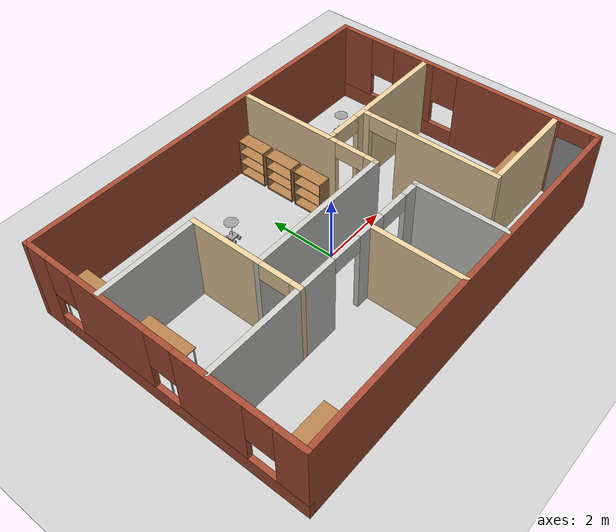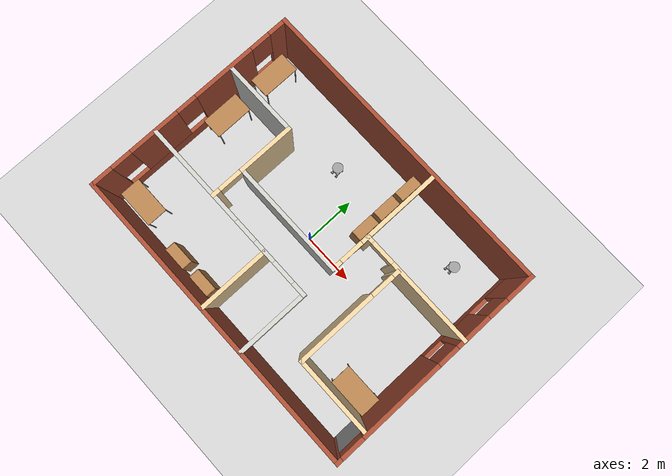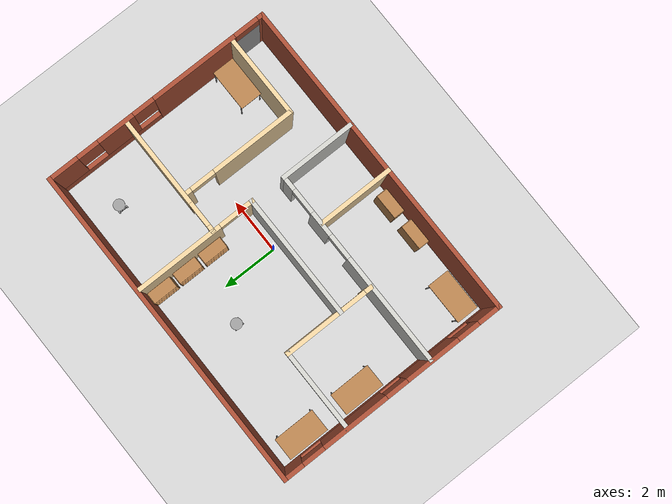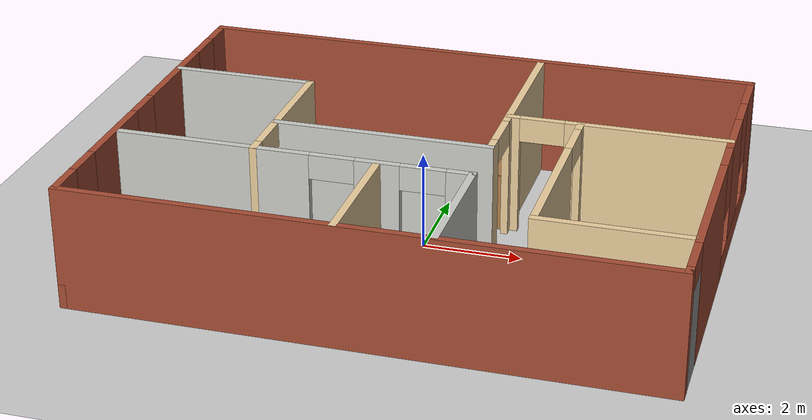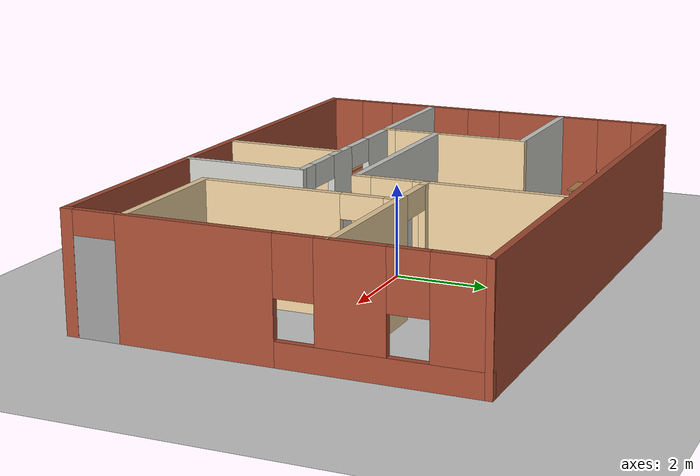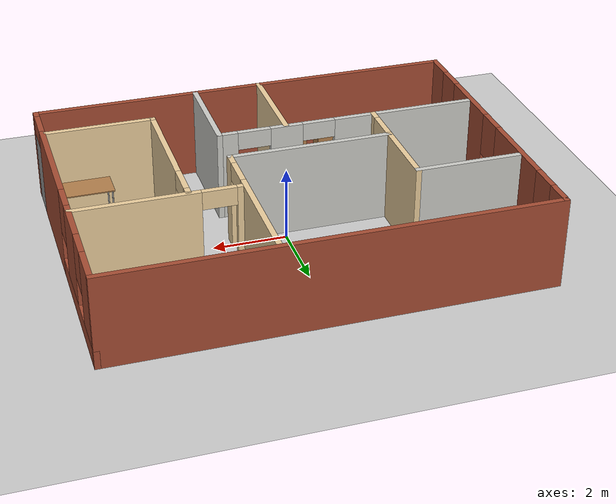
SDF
<sdf version="1.6">
 <world name="default">
  <plugin name="welcome" filename="libwelcome.so"/>
  <light name="sun" type="directional">
   <pose>0 0 10 0 -0 0</pose>
   <diffuse>0.8 0.8 0.8 1</diffuse>
   <specular>0.2 0.2 0.2 1</specular>
   <attenuation>
    <range>1000</range>
    <constant>0.9</constant>
    <linear>0.01</linear>
    <quadratic>0.001</quadratic>
   </attenuation>
   <direction>-0.5 0.1 -0.9</direction>
  </light>
  <model name="ground_plane">
   <static>1</static>
   <link name="link">
    <collision name="collision">
     <geometry><plane><normal>0 0 1</normal><size>100 100</size></plane></geometry>
     <surface><friction><ode><mu>100</mu><mu2>50</mu2></ode></friction></surface>
    </collision>
    <visual name="visual">
     <cast_shadows>0</cast_shadows>
     <geometry><plane><normal>0 0 1</normal><size>100 100</size></plane></geometry>
     <material>
      <script><uri>file://media/materials/scripts/gazebo.material</uri><name>Gazebo/Grey</name></script>
     </material>
    </visual>
   </link>
  </model>
  <gravity>0 0 -9.8</gravity>
  <magnetic_field>6e-06 2.3e-05 -4.2e-05</magnetic_field>
  <atmosphere type="adiabatic"/>
  <physics name="default_physics" default="0" type="ode">
   <max_step_size>0.001</max_step_size>
   <real_time_factor>1</real_time_factor>
   <real_time_update_rate>1000</real_time_update_rate>
  </physics>
  <scene><ambient>0.4 0.4 0.4 1</ambient><background>0.7 0.7 0.7 1</background><shadows>1</shadows></scene>
  <spherical_coordinates>
   <surface_model>EARTH_WGS84</surface_model>
   <latitude_deg>0</latitude_deg>
   <longitude_deg>0</longitude_deg>
   <elevation>0</elevation>
   <heading_deg>0</heading_deg>
  </spherical_coordinates>
  <model name="myplace">
   <link name="Wall_104">
    <pose>3.62551 1.22565 0 0 -0 3.14159</pose>
    <visual name="Wall_104_Visual_0">
     <pose>-0.587051 0 1.25 0 -0 0</pose>
     <geometry><box><size>3.3259 0.15 2.5</size></box></geometry>
     <material>
      <script><uri>file://media/materials/scripts/gazebo.material</uri><name>Gazebo/Grey</name></script>
      <ambient>0.921569 0.807843 0.615686 1</ambient>
     </material>
     <meta><layer>0</layer></meta>
    </visual>
    <collision name="Wall_104_Collision_0">
     <geometry><box><size>3.3259 0.15 2.5</size></box></geometry>
     <pose>-0.587051 0 1.25 0 -0 0</pose>
    </collision>
    <visual name="Wall_104_Visual_1">
     <pose>2.11295 0 1.25 0 -0 0</pose>
     <geometry><box><size>0.274103 0.15 2.5</size></box></geometry>
     <material>
      <script><uri>file://media/materials/scripts/gazebo.material</uri><name>Gazebo/Grey</name></script>
      <ambient>0.921569 0.807843 0.615686 1</ambient>
     </material>
     <meta><layer>0</layer></meta>
    </visual>
    <collision name="Wall_104_Collision_1">
     <geometry><box><size>0.274103 0.15 2.5</size></box></geometry>
     <pose>2.11295 0 1.25 0 -0 0</pose>
    </collision>
    <visual name="Wall_104_Visual_2">
     <pose>1.5259 0 2.25 0 -0 0</pose>
     <geometry><box><size>0.9 0.15 0.5</size></box></geometry>
     <material>
      <script><uri>file://media/materials/scripts/gazebo.material</uri><name>Gazebo/Grey</name></script>
      <ambient>0.921569 0.807843 0.615686 1</ambient>
     </material>
     <meta><layer>0</layer></meta>
    </visual>
    <collision name="Wall_104_Collision_2">
     <geometry><box><size>0.9 0.15 0.5</size></box></geometry>
     <pose>1.5259 0 2.25 0 -0 0</pose>
    </collision>
   </link>
   <link name="Wall_106">
    <pose>2.86292 -0.893742 0 0 0 -1.5708</pose>
    <visual name="Wall_106_Visual_0">
     <pose>-1.98867 0 1.25 0 -0 0</pose>
     <geometry><box><size>0.272657 0.15 2.5</size></box></geometry>
     <material>
      <script><uri>file://media/materials/scripts/gazebo.material</uri><name>Gazebo/Grey</name></script>
      <ambient>0.921569 0.807843 0.615686 1</ambient>
     </material>
     <meta><layer>0</layer></meta>
    </visual>
    <collision name="Wall_106_Collision_0">
     <geometry><box><size>0.272657 0.15 2.5</size></box></geometry>
     <pose>-1.98867 0 1.25 0 -0 0</pose>
    </collision>
    <visual name="Wall_106_Visual_1">
     <pose>0.586329 0 1.25 0 -0 0</pose>
     <geometry><box><size>3.07734 0.15 2.5</size></box></geometry>
     <material>
      <script><uri>file://media/materials/scripts/gazebo.material</uri><name>Gazebo/Grey</name></script>
      <ambient>0.921569 0.807843 0.615686 1</ambient>
     </material>
     <meta><layer>0</layer></meta>
    </visual>
    <collision name="Wall_106_Collision_1">
     <geometry><box><size>3.07734 0.15 2.5</size></box></geometry>
     <pose>0.586329 0 1.25 0 -0 0</pose>
    </collision>
    <visual name="Wall_106_Visual_2">
     <pose>-1.40234 0 2.25 0 -0 0</pose>
     <geometry><box><size>0.9 0.15 0.5</size></box></geometry>
     <material>
      <script><uri>file://media/materials/scripts/gazebo.material</uri><name>Gazebo/Grey</name></script>
      <ambient>0.921569 0.807843 0.615686 1</ambient>
     </material>
     <meta><layer>0</layer></meta>
    </visual>
    <collision name="Wall_106_Collision_2">
     <geometry><box><size>0.9 0.15 0.5</size></box></geometry>
     <pose>-1.40234 0 2.25 0 -0 0</pose>
    </collision>
   </link>
   <link name="Wall_114">
    <collision name="Wall_114_Collision">
     <geometry><box><size>3 0.15 2.5</size></box></geometry>
     <pose>0 0 1.25 0 -0 0</pose>
    </collision>
    <visual name="Wall_114_Visual">
     <pose>0 0 1.25 0 -0 0</pose>
     <geometry><box><size>3 0.15 2.5</size></box></geometry>
     <material>
      <script><uri>file://media/materials/scripts/gazebo.material</uri><name>Gazebo/Grey</name></script>
      <ambient>0.921569 0.807843 0.615686 1</ambient>
     </material>
     <meta><layer>0</layer></meta>
    </visual>
    <pose>4.28792 -2.94374 0 0 -0 0</pose>
   </link>
   <link name="Wall_47">
    <pose>-2.18696 -1.52463 0 0 -0 3.14159</pose>
    <visual name="Wall_47_Visual_0">
     <pose>-3.35943 0 1.25 0 -0 0</pose>
     <geometry><box><size>0.574323 0.15 2.5</size></box></geometry>
     <material>
      <script><uri>file://media/materials/scripts/gazebo.material</uri><name>Gazebo/CeilingTiled</name></script>
      <ambient>0.921569 0.807843 0.615686 1</ambient>
     </material>
     <meta><layer>0</layer></meta>
    </visual>
    <collision name="Wall_47_Collision_0">
     <geometry><box><size>0.574323 0.15 2.5</size></box></geometry>
     <pose>-3.35943 0 1.25 0 -0 0</pose>
    </collision>
    <visual name="Wall_47_Visual_1">
     <pose>-1.72463 0 1.25 0 -0 0</pose>
     <geometry><box><size>0.89527 0.15 2.5</size></box></geometry>
     <material>
      <script><uri>file://media/materials/scripts/gazebo.material</uri><name>Gazebo/CeilingTiled</name></script>
      <ambient>0.921569 0.807843 0.615686 1</ambient>
     </material>
     <meta><layer>0</layer></meta>
    </visual>
    <collision name="Wall_47_Collision_1">
     <geometry><box><size>0.89527 0.15 2.5</size></box></geometry>
     <pose>-1.72463 0 1.25 0 -0 0</pose>
    </collision>
    <visual name="Wall_47_Visual_2">
     <pose>1.6348 0 1.25 0 -0 0</pose>
     <geometry><box><size>4.02359 0.15 2.5</size></box></geometry>
     <material>
      <script><uri>file://media/materials/scripts/gazebo.material</uri><name>Gazebo/CeilingTiled</name></script>
      <ambient>0.921569 0.807843 0.615686 1</ambient>
     </material>
     <meta><layer>0</layer></meta>
    </visual>
    <collision name="Wall_47_Collision_2">
     <geometry><box><size>4.02359 0.15 2.5</size></box></geometry>
     <pose>1.6348 0 1.25 0 -0 0</pose>
    </collision>
    <visual name="Wall_47_Visual_3">
     <pose>-2.62227 0 2.25 0 -0 0</pose>
     <geometry><box><size>0.9 0.15 0.5</size></box></geometry>
     <material>
      <script><uri>file://media/materials/scripts/gazebo.material</uri><name>Gazebo/CeilingTiled</name></script>
      <ambient>0.921569 0.807843 0.615686 1</ambient>
     </material>
     <meta><layer>0</layer></meta>
    </visual>
    <collision name="Wall_47_Collision_3">
     <geometry><box><size>0.9 0.15 0.5</size></box></geometry>
     <pose>-2.62227 0 2.25 0 -0 0</pose>
    </collision>
    <visual name="Wall_47_Visual_4">
     <pose>-0.827 0 2.25 0 -0 0</pose>
     <geometry><box><size>0.9 0.15 0.5</size></box></geometry>
     <material>
      <script><uri>file://media/materials/scripts/gazebo.material</uri><name>Gazebo/CeilingTiled</name></script>
      <ambient>0.921569 0.807843 0.615686 1</ambient>
     </material>
     <meta><layer>0</layer></meta>
    </visual>
    <collision name="Wall_47_Collision_4">
     <geometry><box><size>0.9 0.15 0.5</size></box></geometry>
     <pose>-0.827 0 2.25 0 -0 0</pose>
    </collision>
   </link>
   <link name="Wall_49">
    <pose>-5.82011 0 0 0 0 -1.5708</pose>
    <visual name="Wall_49_Visual_0">
     <pose>-3.85497 0 1.25 0 -0 0</pose>
     <geometry><box><size>0.790055 0.15 2.5</size></box></geometry>
     <material>
      <script><uri>file://media/materials/scripts/gazebo.material</uri><name>Gazebo/Bricks</name></script>
      <ambient>1 1 1 1</ambient>
     </material>
     <meta><layer>0</layer></meta>
    </visual>
    <collision name="Wall_49_Collision_0">
     <geometry><box><size>0.790055 0.15 2.5</size></box></geometry>
     <pose>-3.85497 0 1.25 0 -0 0</pose>
    </collision>
    <visual name="Wall_49_Visual_1">
     <pose>0.395028 0 0.25 0 -0 0</pose>
     <geometry><box><size>7.70995 0.15 0.5</size></box></geometry>
     <material>
      <script><uri>file://media/materials/scripts/gazebo.material</uri><name>Gazebo/Bricks</name></script>
      <ambient>1 1 1 1</ambient>
     </material>
     <meta><layer>0</layer></meta>
    </visual>
    <collision name="Wall_49_Collision_1">
     <geometry><box><size>7.70995 0.15 0.5</size></box></geometry>
     <pose>0.395028 0 0.25 0 -0 0</pose>
    </collision>
    <visual name="Wall_49_Visual_2">
     <pose>-1.4408 0 1.5 0 -0 0</pose>
     <geometry><box><size>2.43829 0.15 2</size></box></geometry>
     <material>
      <script><uri>file://media/materials/scripts/gazebo.material</uri><name>Gazebo/Bricks</name></script>
      <ambient>1 1 1 1</ambient>
     </material>
     <meta><layer>0</layer></meta>
    </visual>
    <collision name="Wall_49_Collision_2">
     <geometry><box><size>2.43829 0.15 2</size></box></geometry>
     <pose>-1.4408 0 1.5 0 -0 0</pose>
    </collision>
    <visual name="Wall_49_Visual_3">
     <pose>1.57623 0 1.5 0 -0 0</pose>
     <geometry><box><size>1.99579 0.15 2</size></box></geometry>
     <material>
      <script><uri>file://media/materials/scripts/gazebo.material</uri><name>Gazebo/Bricks</name></script>
      <ambient>1 1 1 1</ambient>
     </material>
     <meta><layer>0</layer></meta>
    </visual>
    <collision name="Wall_49_Collision_3">
     <geometry><box><size>1.99579 0.15 2</size></box></geometry>
     <pose>1.57623 0 1.5 0 -0 0</pose>
    </collision>
    <visual name="Wall_49_Visual_4">
     <pose>3.81206 0 1.5 0 -0 0</pose>
     <geometry><box><size>0.875873 0.15 2</size></box></geometry>
     <material>
      <script><uri>file://media/materials/scripts/gazebo.material</uri><name>Gazebo/Bricks</name></script>
      <ambient>1 1 1 1</ambient>
     </material>
     <meta><layer>0</layer></meta>
    </visual>
    <collision name="Wall_49_Collision_4">
     <geometry><box><size>0.875873 0.15 2</size></box></geometry>
     <pose>3.81206 0 1.5 0 -0 0</pose>
    </collision>
    <visual name="Wall_49_Visual_5">
     <pose>-3.05994 0 1.9 0 -0 0</pose>
     <geometry><box><size>0.8 0.15 1.2</size></box></geometry>
     <material>
      <script><uri>file://media/materials/scripts/gazebo.material</uri><name>Gazebo/Bricks</name></script>
      <ambient>1 1 1 1</ambient>
     </material>
     <meta><layer>0</layer></meta>
    </visual>
    <collision name="Wall_49_Collision_5">
     <geometry><box><size>0.8 0.15 1.2</size></box></geometry>
     <pose>-3.05994 0 1.9 0 -0 0</pose>
    </collision>
    <visual name="Wall_49_Visual_6">
     <pose>0.17834 0 1.9 0 -0 0</pose>
     <geometry><box><size>0.8 0.15 1.2</size></box></geometry>
     <material>
      <script><uri>file://media/materials/scripts/gazebo.material</uri><name>Gazebo/Bricks</name></script>
      <ambient>1 1 1 1</ambient>
     </material>
     <meta><layer>0</layer></meta>
    </visual>
    <collision name="Wall_49_Collision_6">
     <geometry><box><size>0.8 0.15 1.2</size></box></geometry>
     <pose>0.17834 0 1.9 0 -0 0</pose>
    </collision>
    <visual name="Wall_49_Visual_7">
     <pose>2.97413 0 1.9 0 -0 0</pose>
     <geometry><box><size>0.8 0.15 1.2</size></box></geometry>
     <material>
      <script><uri>file://media/materials/scripts/gazebo.material</uri><name>Gazebo/Bricks</name></script>
      <ambient>1 1 1 1</ambient>
     </material>
     <meta><layer>0</layer></meta>
    </visual>
    <collision name="Wall_49_Collision_7">
     <geometry><box><size>0.8 0.15 1.2</size></box></geometry>
     <pose>2.97413 0 1.9 0 -0 0</pose>
    </collision>
   </link>
   <link name="Wall_53">
    <pose>5.82011 0 0 0 -0 1.5708</pose>
    <visual name="Wall_53_Visual_0">
     <pose>-4.11865 0 1.25 0 -0 0</pose>
     <geometry><box><size>0.262693 0.15 2.5</size></box></geometry>
     <material>
      <script><uri>file://media/materials/scripts/gazebo.material</uri><name>Gazebo/Bricks</name></script>
      <ambient>1 1 1 1</ambient>
     </material>
     <meta><layer>0</layer></meta>
    </visual>
    <collision name="Wall_53_Collision_0">
     <geometry><box><size>0.262693 0.15 2.5</size></box></geometry>
     <pose>-4.11865 0 1.25 0 -0 0</pose>
    </collision>
    <visual name="Wall_53_Visual_1">
     <pose>-1.48084 0 1.25 0 -0 0</pose>
     <geometry><box><size>3.21294 0.15 2.5</size></box></geometry>
     <material>
      <script><uri>file://media/materials/scripts/gazebo.material</uri><name>Gazebo/Bricks</name></script>
      <ambient>1 1 1 1</ambient>
     </material>
     <meta><layer>0</layer></meta>
    </visual>
    <collision name="Wall_53_Collision_1">
     <geometry><box><size>3.21294 0.15 2.5</size></box></geometry>
     <pose>-1.48084 0 1.25 0 -0 0</pose>
    </collision>
    <visual name="Wall_53_Visual_2">
     <pose>2.18782 0 0.25 0 -0 0</pose>
     <geometry><box><size>4.12437 0.15 0.5</size></box></geometry>
     <material>
      <script><uri>file://media/materials/scripts/gazebo.material</uri><name>Gazebo/Bricks</name></script>
      <ambient>1 1 1 1</ambient>
     </material>
     <meta><layer>0</layer></meta>
    </visual>
    <collision name="Wall_53_Collision_2">
     <geometry><box><size>4.12437 0.15 0.5</size></box></geometry>
     <pose>2.18782 0 0.25 0 -0 0</pose>
    </collision>
    <visual name="Wall_53_Visual_3">
     <pose>1.61177 0 1.5 0 -0 0</pose>
     <geometry><box><size>1.37227 0.15 2</size></box></geometry>
     <material>
      <script><uri>file://media/materials/scripts/gazebo.material</uri><name>Gazebo/Bricks</name></script>
      <ambient>1 1 1 1</ambient>
     </material>
     <meta><layer>0</layer></meta>
    </visual>
    <collision name="Wall_53_Collision_3">
     <geometry><box><size>1.37227 0.15 2</size></box></geometry>
     <pose>1.61177 0 1.5 0 -0 0</pose>
    </collision>
    <visual name="Wall_53_Visual_4">
     <pose>3.67395 0 1.5 0 -0 0</pose>
     <geometry><box><size>1.1521 0.15 2</size></box></geometry>
     <material>
      <script><uri>file://media/materials/scripts/gazebo.material</uri><name>Gazebo/Bricks</name></script>
      <ambient>1 1 1 1</ambient>
     </material>
     <meta><layer>0</layer></meta>
    </visual>
    <collision name="Wall_53_Collision_4">
     <geometry><box><size>1.1521 0.15 2</size></box></geometry>
     <pose>3.67395 0 1.5 0 -0 0</pose>
    </collision>
    <visual name="Wall_53_Visual_5">
     <pose>0.525634 0 1.9 0 -0 0</pose>
     <geometry><box><size>0.8 0.15 1.2</size></box></geometry>
     <material>
      <script><uri>file://media/materials/scripts/gazebo.material</uri><name>Gazebo/Bricks</name></script>
      <ambient>1 1 1 1</ambient>
     </material>
     <meta><layer>0</layer></meta>
    </visual>
    <collision name="Wall_53_Collision_5">
     <geometry><box><size>0.8 0.15 1.2</size></box></geometry>
     <pose>0.525634 0 1.9 0 -0 0</pose>
    </collision>
    <visual name="Wall_53_Visual_6">
     <pose>2.6979 0 1.9 0 -0 0</pose>
     <geometry><box><size>0.8 0.15 1.2</size></box></geometry>
     <material>
      <script><uri>file://media/materials/scripts/gazebo.material</uri><name>Gazebo/Bricks</name></script>
      <ambient>1 1 1 1</ambient>
     </material>
     <meta><layer>0</layer></meta>
    </visual>
    <collision name="Wall_53_Collision_6">
     <geometry><box><size>0.8 0.15 1.2</size></box></geometry>
     <pose>2.6979 0 1.9 0 -0 0</pose>
    </collision>
    <visual name="Wall_53_Visual_7">
     <pose>-3.53731 0 2.25 0 -0 0</pose>
     <geometry><box><size>0.9 0.15 0.5</size></box></geometry>
     <material>
      <script><uri>file://media/materials/scripts/gazebo.material</uri><name>Gazebo/Bricks</name></script>
      <ambient>1 1 1 1</ambient>
     </material>
     <meta><layer>0</layer></meta>
    </visual>
    <collision name="Wall_53_Collision_7">
     <geometry><box><size>0.9 0.15 0.5</size></box></geometry>
     <pose>-3.53731 0 2.25 0 -0 0</pose>
    </collision>
   </link>
   <link name="Wall_63">
    <pose>-2.92989 0.111193 0 0 0 -1.5708</pose>
    <visual name="Wall_63_Visual_0">
     <pose>-0.619935 0 1.25 0 -0 0</pose>
     <geometry><box><size>2.18258 0.15 2.5</size></box></geometry>
     <material>
      <script><uri>file://media/materials/scripts/gazebo.material</uri><name>Gazebo/Grey</name></script>
      <ambient>0.921569 0.807843 0.615686 1</ambient>
     </material>
     <meta><layer>0</layer></meta>
    </visual>
    <collision name="Wall_63_Collision_0">
     <geometry><box><size>2.18258 0.15 2.5</size></box></geometry>
     <pose>-0.619935 0 1.25 0 -0 0</pose>
    </collision>
    <visual name="Wall_63_Visual_1">
     <pose>1.54129 0 1.25 0 -0 0</pose>
     <geometry><box><size>0.33987 0.15 2.5</size></box></geometry>
     <material>
      <script><uri>file://media/materials/scripts/gazebo.material</uri><name>Gazebo/Grey</name></script>
      <ambient>0.921569 0.807843 0.615686 1</ambient>
     </material>
     <meta><layer>0</layer></meta>
    </visual>
    <collision name="Wall_63_Collision_1">
     <geometry><box><size>0.33987 0.15 2.5</size></box></geometry>
     <pose>1.54129 0 1.25 0 -0 0</pose>
    </collision>
    <visual name="Wall_63_Visual_2">
     <pose>0.921354 0 2.25 0 -0 0</pose>
     <geometry><box><size>0.9 0.15 0.5</size></box></geometry>
     <material>
      <script><uri>file://media/materials/scripts/gazebo.material</uri><name>Gazebo/Grey</name></script>
      <ambient>0.921569 0.807843 0.615686 1</ambient>
     </material>
     <meta><layer>0</layer></meta>
    </visual>
    <collision name="Wall_63_Collision_2">
     <geometry><box><size>0.9 0.15 0.5</size></box></geometry>
     <pose>0.921354 0 2.25 0 -0 0</pose>
    </collision>
   </link>
   <link name="Wall_65">
    <collision name="Wall_65_Collision">
     <geometry><box><size>2.75 0.15 2.5</size></box></geometry>
     <pose>0 0 1.25 0 -0 0</pose>
    </collision>
    <visual name="Wall_65_Visual">
     <pose>0 0 1.25 0 -0 0</pose>
     <geometry><box><size>2.75 0.15 2.5</size></box></geometry>
     <material>
      <script><uri>file://media/materials/scripts/gazebo.material</uri><name>Gazebo/CeilingTiled</name></script>
      <ambient>0.921569 0.807843 0.615686 1</ambient>
     </material>
     <meta><layer>0</layer></meta>
    </visual>
    <pose>1.38463 -2.82463 0 0 0 -1.5708</pose>
   </link>
   <link name="Wall_68">
    <collision name="Wall_68_Collision">
     <geometry><box><size>2.75 0.15 2.5</size></box></geometry>
     <pose>0 0 1.25 0 -0 0</pose>
    </collision>
    <visual name="Wall_68_Visual">
     <pose>0 0 1.25 0 -0 0</pose>
     <geometry><box><size>2.75 0.15 2.5</size></box></geometry>
     <material>
      <script><uri>file://media/materials/scripts/gazebo.material</uri><name>Gazebo/Grey</name></script>
      <ambient>0.921569 0.807843 0.615686 1</ambient>
     </material>
     <meta><layer>0</layer></meta>
    </visual>
    <pose>-0.456438 -2.86618 0 0 0 -1.5708</pose>
   </link>
   <link name="Wall_71">
    <collision name="Wall_71_Collision">
     <geometry><box><size>4.5 0.15 2.5</size></box></geometry>
     <pose>0 0 1.25 0 -0 0</pose>
    </collision>
    <visual name="Wall_71_Visual">
     <pose>0 0 1.25 0 -0 0</pose>
     <geometry><box><size>4.5 0.15 2.5</size></box></geometry>
     <material>
      <script><uri>file://media/materials/scripts/gazebo.material</uri><name>Gazebo/CeilingTiled</name></script>
      <ambient>0.921569 0.807843 0.615686 1</ambient>
     </material>
     <meta><layer>0</layer></meta>
    </visual>
    <pose>-0.757802 -0.286519 0 0 -0 3.14159</pose>
   </link>
   <link name="Wall_78">
    <collision name="Wall_78_Collision">
     <geometry><box><size>3 0.15 2.5</size></box></geometry>
     <pose>0 0 1.25 0 -0 0</pose>
    </collision>
    <visual name="Wall_78_Visual">
     <pose>0 0 1.25 0 -0 0</pose>
     <geometry><box><size>3 0.15 2.5</size></box></geometry>
     <material>
      <script><uri>file://media/materials/scripts/gazebo.material</uri><name>Gazebo/CeilingTiled</name></script>
      <ambient>0.921569 0.807843 0.615686 1</ambient>
     </material>
     <meta><layer>0</layer></meta>
    </visual>
    <pose>-4.35489 1.74738 0 0 -0 3.14159</pose>
   </link>
   <link name="Wall_80">
    <collision name="Wall_80_Collision">
     <geometry><box><size>11.7902 0.15 2.5</size></box></geometry>
     <pose>0 0 1.25 0 -0 0</pose>
    </collision>
    <visual name="Wall_80_Visual">
     <pose>0 0 1.25 0 -0 0</pose>
     <geometry><box><size>11.7902 0.15 2.5</size></box></geometry>
     <material>
      <script><uri>file://media/materials/scripts/gazebo.material</uri><name>Gazebo/Bricks</name></script>
      <ambient>1 1 1 1</ambient>
     </material>
     <meta><layer>0</layer></meta>
    </visual>
    <pose>0 4.175 0 0 -0 0</pose>
   </link>
   <link name="Wall_82">
    <collision name="Wall_82_Collision">
     <geometry><box><size>11.7902 0.15 2.5</size></box></geometry>
     <pose>0 0 1.25 0 -0 0</pose>
    </collision>
    <visual name="Wall_82_Visual">
     <pose>0 0 1.25 0 -0 0</pose>
     <geometry><box><size>11.7902 0.15 2.5</size></box></geometry>
     <material>
      <script><uri>file://media/materials/scripts/gazebo.material</uri><name>Gazebo/Bricks</name></script>
      <ambient>1 1 1 1</ambient>
     </material>
     <meta><layer>0</layer></meta>
    </visual>
    <pose>0 -4.175 0 0 -0 0</pose>
   </link>
   <link name="Wall_89">
    <pose>1.4172 1.88848 0 0 -0 1.5708</pose>
    <visual name="Wall_89_Visual_0">
     <pose>-2.03994 0 1.25 0 -0 0</pose>
     <geometry><box><size>0.42012 0.15 2.5</size></box></geometry>
     <material>
      <script><uri>file://media/materials/scripts/gazebo.material</uri><name>Gazebo/Grey</name></script>
      <ambient>0.921569 0.807843 0.615686 1</ambient>
     </material>
     <meta><layer>0</layer></meta>
    </visual>
    <collision name="Wall_89_Collision_0">
     <geometry><box><size>0.42012 0.15 2.5</size></box></geometry>
     <pose>-2.03994 0 1.25 0 -0 0</pose>
    </collision>
    <visual name="Wall_89_Visual_1">
     <pose>0.66006 0 1.25 0 -0 0</pose>
     <geometry><box><size>3.17988 0.15 2.5</size></box></geometry>
     <material>
      <script><uri>file://media/materials/scripts/gazebo.material</uri><name>Gazebo/Grey</name></script>
      <ambient>0.921569 0.807843 0.615686 1</ambient>
     </material>
     <meta><layer>0</layer></meta>
    </visual>
    <collision name="Wall_89_Collision_1">
     <geometry><box><size>3.17988 0.15 2.5</size></box></geometry>
     <pose>0.66006 0 1.25 0 -0 0</pose>
    </collision>
    <visual name="Wall_89_Visual_2">
     <pose>-1.37988 0 2.25 0 -0 0</pose>
     <geometry><box><size>0.9 0.15 0.5</size></box></geometry>
     <material>
      <script><uri>file://media/materials/scripts/gazebo.material</uri><name>Gazebo/Grey</name></script>
      <ambient>0.921569 0.807843 0.615686 1</ambient>
     </material>
     <meta><layer>0</layer></meta>
    </visual>
    <collision name="Wall_89_Collision_2">
     <geometry><box><size>0.9 0.15 0.5</size></box></geometry>
     <pose>-1.37988 0 2.25 0 -0 0</pose>
    </collision>
   </link>
   <static>1</static>
  </model>
  <model name="table">
   <static>1</static>
   <link name="link">
    <collision name="surface">
     <pose>0 0 1 0 -0 0</pose>
     <geometry><box><size>1.5 0.8 0.03</size></box></geometry>
     <surface><friction><ode><mu>0.6</mu><mu2>0.6</mu2></ode></friction></surface>
    </collision>
    <visual name="visual1">
     <pose>0 0 1 0 -0 0</pose>
     <geometry><box><size>1.5 0.8 0.03</size></box></geometry>
     <material>
      <script><uri>file://media/materials/scripts/gazebo.material</uri><name>Gazebo/Wood</name></script>
     </material>
    </visual>
    <collision name="front_left_leg">
     <pose>0.68 0.38 0.5 0 -0 0</pose>
     <geometry><cylinder><radius>0.02</radius><length>1</length></cylinder></geometry>
    </collision>
    <visual name="front_left_leg">
     <pose>0.68 0.38 0.5 0 -0 0</pose>
     <geometry><cylinder><radius>0.02</radius><length>1</length></cylinder></geometry>
     <material>
      <script><uri>file://media/materials/scripts/gazebo.material</uri><name>Gazebo/Grey</name></script>
     </material>
    </visual>
    <collision name="front_right_leg">
     <pose>0.68 -0.38 0.5 0 -0 0</pose>
     <geometry><cylinder><radius>0.02</radius><length>1</length></cylinder></geometry>
    </collision>
    <visual name="front_right_leg">
     <pose>0.68 -0.38 0.5 0 -0 0</pose>
     <geometry><cylinder><radius>0.02</radius><length>1</length></cylinder></geometry>
     <material>
      <script><uri>file://media/materials/scripts/gazebo.material</uri><name>Gazebo/Grey</name></script>
     </material>
    </visual>
    <collision name="back_right_leg">
     <pose>-0.68 -0.38 0.5 0 -0 0</pose>
     <geometry><cylinder><radius>0.02</radius><length>1</length></cylinder></geometry>
    </collision>
    <visual name="back_right_leg">
     <pose>-0.68 -0.38 0.5 0 -0 0</pose>
     <geometry><cylinder><radius>0.02</radius><length>1</length></cylinder></geometry>
     <material>
      <script><uri>file://media/materials/scripts/gazebo.material</uri><name>Gazebo/Grey</name></script>
     </material>
    </visual>
    <collision name="back_left_leg">
     <pose>-0.68 0.38 0.5 0 -0 0</pose>
     <geometry><cylinder><radius>0.02</radius><length>1</length></cylinder></geometry>
    </collision>
    <visual name="back_left_leg">
     <pose>-0.68 0.38 0.5 0 -0 0</pose>
     <geometry><cylinder><radius>0.02</radius><length>1</length></cylinder></geometry>
     <material>
      <script><uri>file://media/materials/scripts/gazebo.material</uri><name>Gazebo/Grey</name></script>
     </material>
    </visual>
   </link>
   <pose>-5.2 3 0 0 -0 1.5707</pose>
  </model>
  <model name="bookshelf">
   <static>1</static>
   <link name="link">
    <inertial><mass>1</mass></inertial>
    <collision name="back">
     <pose>0 0.005 0.6 0 -0 0</pose>
     <geometry><box><size>0.9 0.01 1.2</size></box></geometry>
    </collision>
    <visual name="visual1">
     <pose>0 0.005 0.6 0 -0 0</pose>
     <geometry><box><size>0.9 0.01 1.2</size></box></geometry>
     <material>
      <script><uri>file://media/materials/scripts/gazebo.material</uri><name>Gazebo/Wood</name></script>
     </material>
    </visual>
    <collision name="left_side">
     <pose>0.45 -0.195 0.6 0 -0 0</pose>
     <geometry><box><size>0.02 0.4 1.2</size></box></geometry>
    </collision>
    <visual name="visual2">
     <pose>0.45 -0.195 0.6 0 -0 0</pose>
     <geometry><box><size>0.02 0.4 1.2</size></box></geometry>
     <material>
      <script><uri>file://media/materials/scripts/gazebo.material</uri><name>Gazebo/Wood</name></script>
     </material>
    </visual>
    <collision name="right_side">
     <pose>-0.45 -0.195 0.6 0 -0 0</pose>
     <geometry><box><size>0.02 0.4 1.2</size></box></geometry>
    </collision>
    <visual name="visual3">
     <pose>-0.45 -0.195 0.6 0 -0 0</pose>
     <geometry><box><size>0.02 0.4 1.2</size></box></geometry>
     <material>
      <script><uri>file://media/materials/scripts/gazebo.material</uri><name>Gazebo/Wood</name></script>
     </material>
    </visual>
    <collision name="bottom">
     <pose>0 -0.195 0.03 0 -0 0</pose>
     <geometry><box><size>0.88 0.4 0.06</size></box></geometry>
    </collision>
    <visual name="visual4">
     <pose>0 -0.195 0.03 0 -0 0</pose>
     <geometry><box><size>0.88 0.4 0.06</size></box></geometry>
     <material>
      <script><uri>file://media/materials/scripts/gazebo.material</uri><name>Gazebo/Wood</name></script>
     </material>
    </visual>
    <collision name="top">
     <pose>0 -0.195 1.19 0 -0 0</pose>
     <geometry><box><size>0.88 0.4 0.02</size></box></geometry>
    </collision>
    <visual name="visual5">
     <pose>0 -0.195 1.19 0 -0 0</pose>
     <geometry><box><size>0.88 0.4 0.02</size></box></geometry>
     <material>
      <script><uri>file://media/materials/scripts/gazebo.material</uri><name>Gazebo/Wood</name></script>
     </material>
    </visual>
    <collision name="low_shelf">
     <pose>0 -0.195 0.43 0 -0 0</pose>
     <geometry><box><size>0.88 0.4 0.02</size></box></geometry>
    </collision>
    <visual name="visual6">
     <pose>0 -0.195 0.43 0 -0 0</pose>
     <geometry><box><size>0.88 0.4 0.02</size></box></geometry>
     <material>
      <script><uri>file://media/materials/scripts/gazebo.material</uri><name>Gazebo/Wood</name></script>
     </material>
    </visual>
    <collision name="high_shelf">
     <pose>0 -0.195 0.8 0 -0 0</pose>
     <geometry><box><size>0.88 0.4 0.02</size></box></geometry>
    </collision>
    <visual name="visual7">
     <pose>0 -0.195 0.8 0 -0 0</pose>
     <geometry><box><size>0.88 0.4 0.02</size></box></geometry>
     <material>
      <script><uri>file://media/materials/scripts/gazebo.material</uri><name>Gazebo/Wood</name></script>
     </material>
    </visual>
   </link>
   <pose>1.3 3.63049 0 0 0 -1.57119</pose>
  </model>
  <model name="bookshelf_clone">
   <static>1</static>
   <link name="link">
    <inertial><mass>1</mass></inertial>
    <collision name="back">
     <pose>0 0.005 0.6 0 -0 0</pose>
     <geometry><box><size>0.9 0.01 1.2</size></box></geometry>
    </collision>
    <visual name="visual1">
     <pose>0 0.005 0.6 0 -0 0</pose>
     <geometry><box><size>0.9 0.01 1.2</size></box></geometry>
     <material>
      <script><uri>file://media/materials/scripts/gazebo.material</uri><name>Gazebo/Wood</name></script>
     </material>
    </visual>
    <collision name="left_side">
     <pose>0.45 -0.195 0.6 0 -0 0</pose>
     <geometry><box><size>0.02 0.4 1.2</size></box></geometry>
    </collision>
    <visual name="visual2">
     <pose>0.45 -0.195 0.6 0 -0 0</pose>
     <geometry><box><size>0.02 0.4 1.2</size></box></geometry>
     <material>
      <script><uri>file://media/materials/scripts/gazebo.material</uri><name>Gazebo/Wood</name></script>
     </material>
    </visual>
    <collision name="right_side">
     <pose>-0.45 -0.195 0.6 0 -0 0</pose>
     <geometry><box><size>0.02 0.4 1.2</size></box></geometry>
    </collision>
    <visual name="visual3">
     <pose>-0.45 -0.195 0.6 0 -0 0</pose>
     <geometry><box><size>0.02 0.4 1.2</size></box></geometry>
     <material>
      <script><uri>file://media/materials/scripts/gazebo.material</uri><name>Gazebo/Wood</name></script>
     </material>
    </visual>
    <collision name="bottom">
     <pose>0 -0.195 0.03 0 -0 0</pose>
     <geometry><box><size>0.88 0.4 0.06</size></box></geometry>
    </collision>
    <visual name="visual4">
     <pose>0 -0.195 0.03 0 -0 0</pose>
     <geometry><box><size>0.88 0.4 0.06</size></box></geometry>
     <material>
      <script><uri>file://media/materials/scripts/gazebo.material</uri><name>Gazebo/Wood</name></script>
     </material>
    </visual>
    <collision name="top">
     <pose>0 -0.195 1.19 0 -0 0</pose>
     <geometry><box><size>0.88 0.4 0.02</size></box></geometry>
    </collision>
    <visual name="visual5">
     <pose>0 -0.195 1.19 0 -0 0</pose>
     <geometry><box><size>0.88 0.4 0.02</size></box></geometry>
     <material>
      <script><uri>file://media/materials/scripts/gazebo.material</uri><name>Gazebo/Wood</name></script>
     </material>
    </visual>
    <collision name="low_shelf">
     <pose>0 -0.195 0.43 0 -0 0</pose>
     <geometry><box><size>0.88 0.4 0.02</size></box></geometry>
    </collision>
    <visual name="visual6">
     <pose>0 -0.195 0.43 0 -0 0</pose>
     <geometry><box><size>0.88 0.4 0.02</size></box></geometry>
     <material>
      <script><uri>file://media/materials/scripts/gazebo.material</uri><name>Gazebo/Wood</name></script>
     </material>
    </visual>
    <collision name="high_shelf">
     <pose>0 -0.195 0.8 0 -0 0</pose>
     <geometry><box><size>0.88 0.4 0.02</size></box></geometry>
    </collision>
    <visual name="visual7">
     <pose>0 -0.195 0.8 0 -0 0</pose>
     <geometry><box><size>0.88 0.4 0.02</size></box></geometry>
     <material>
      <script><uri>file://media/materials/scripts/gazebo.material</uri><name>Gazebo/Wood</name></script>
     </material>
    </visual>
   </link>
   <pose>1.30004 2.60838 0 0 0 -1.57119</pose>
  </model>
  <model name="bookshelf_clone_0">
   <static>1</static>
   <link name="link">
    <inertial><mass>1</mass></inertial>
    <collision name="back">
     <pose>0 0.005 0.6 0 -0 0</pose>
     <geometry><box><size>0.9 0.01 1.2</size></box></geometry>
    </collision>
    <visual name="visual1">
     <pose>0 0.005 0.6 0 -0 0</pose>
     <geometry><box><size>0.9 0.01 1.2</size></box></geometry>
     <material>
      <script><uri>file://media/materials/scripts/gazebo.material</uri><name>Gazebo/Wood</name></script>
     </material>
    </visual>
    <collision name="left_side">
     <pose>0.45 -0.195 0.6 0 -0 0</pose>
     <geometry><box><size>0.02 0.4 1.2</size></box></geometry>
    </collision>
    <visual name="visual2">
     <pose>0.45 -0.195 0.6 0 -0 0</pose>
     <geometry><box><size>0.02 0.4 1.2</size></box></geometry>
     <material>
      <script><uri>file://media/materials/scripts/gazebo.material</uri><name>Gazebo/Wood</name></script>
     </material>
    </visual>
    <collision name="right_side">
     <pose>-0.45 -0.195 0.6 0 -0 0</pose>
     <geometry><box><size>0.02 0.4 1.2</size></box></geometry>
    </collision>
    <visual name="visual3">
     <pose>-0.45 -0.195 0.6 0 -0 0</pose>
     <geometry><box><size>0.02 0.4 1.2</size></box></geometry>
     <material>
      <script><uri>file://media/materials/scripts/gazebo.material</uri><name>Gazebo/Wood</name></script>
     </material>
    </visual>
    <collision name="bottom">
     <pose>0 -0.195 0.03 0 -0 0</pose>
     <geometry><box><size>0.88 0.4 0.06</size></box></geometry>
    </collision>
    <visual name="visual4">
     <pose>0 -0.195 0.03 0 -0 0</pose>
     <geometry><box><size>0.88 0.4 0.06</size></box></geometry>
     <material>
      <script><uri>file://media/materials/scripts/gazebo.material</uri><name>Gazebo/Wood</name></script>
     </material>
    </visual>
    <collision name="top">
     <pose>0 -0.195 1.19 0 -0 0</pose>
     <geometry><box><size>0.88 0.4 0.02</size></box></geometry>
    </collision>
    <visual name="visual5">
     <pose>0 -0.195 1.19 0 -0 0</pose>
     <geometry><box><size>0.88 0.4 0.02</size></box></geometry>
     <material>
      <script><uri>file://media/materials/scripts/gazebo.material</uri><name>Gazebo/Wood</name></script>
     </material>
    </visual>
    <collision name="low_shelf">
     <pose>0 -0.195 0.43 0 -0 0</pose>
     <geometry><box><size>0.88 0.4 0.02</size></box></geometry>
    </collision>
    <visual name="visual6">
     <pose>0 -0.195 0.43 0 -0 0</pose>
     <geometry><box><size>0.88 0.4 0.02</size></box></geometry>
     <material>
      <script><uri>file://media/materials/scripts/gazebo.material</uri><name>Gazebo/Wood</name></script>
     </material>
    </visual>
    <collision name="high_shelf">
     <pose>0 -0.195 0.8 0 -0 0</pose>
     <geometry><box><size>0.88 0.4 0.02</size></box></geometry>
    </collision>
    <visual name="visual7">
     <pose>0 -0.195 0.8 0 -0 0</pose>
     <geometry><box><size>0.88 0.4 0.02</size></box></geometry>
     <material>
      <script><uri>file://media/materials/scripts/gazebo.material</uri><name>Gazebo/Wood</name></script>
     </material>
    </visual>
   </link>
   <pose>1.30003 1.59548 0 0 0 -1.57119</pose>
  </model>
  <model name="table_clone">
   <static>1</static>
   <link name="link">
    <collision name="surface">
     <pose>0 0 1 0 -0 0</pose>
     <geometry><box><size>1.5 0.8 0.03</size></box></geometry>
     <surface><friction><ode><mu>0.6</mu><mu2>0.6</mu2></ode></friction></surface>
    </collision>
    <visual name="visual1">
     <pose>0 0 1 0 -0 0</pose>
     <geometry><box><size>1.5 0.8 0.03</size></box></geometry>
     <material>
      <script><uri>file://media/materials/scripts/gazebo.material</uri><name>Gazebo/Wood</name></script>
     </material>
    </visual>
    <collision name="front_left_leg">
     <pose>0.68 0.38 0.5 0 -0 0</pose>
     <geometry><cylinder><radius>0.02</radius><length>1</length></cylinder></geometry>
    </collision>
    <visual name="front_left_leg">
     <pose>0.68 0.38 0.5 0 -0 0</pose>
     <geometry><cylinder><radius>0.02</radius><length>1</length></cylinder></geometry>
     <material>
      <script><uri>file://media/materials/scripts/gazebo.material</uri><name>Gazebo/Grey</name></script>
     </material>
    </visual>
    <collision name="front_right_leg">
     <pose>0.68 -0.38 0.5 0 -0 0</pose>
     <geometry><cylinder><radius>0.02</radius><length>1</length></cylinder></geometry>
    </collision>
    <visual name="front_right_leg">
     <pose>0.68 -0.38 0.5 0 -0 0</pose>
     <geometry><cylinder><radius>0.02</radius><length>1</length></cylinder></geometry>
     <material>
      <script><uri>file://media/materials/scripts/gazebo.material</uri><name>Gazebo/Grey</name></script>
     </material>
    </visual>
    <collision name="back_right_leg">
     <pose>-0.68 -0.38 0.5 0 -0 0</pose>
     <geometry><cylinder><radius>0.02</radius><length>1</length></cylinder></geometry>
    </collision>
    <visual name="back_right_leg">
     <pose>-0.68 -0.38 0.5 0 -0 0</pose>
     <geometry><cylinder><radius>0.02</radius><length>1</length></cylinder></geometry>
     <material>
      <script><uri>file://media/materials/scripts/gazebo.material</uri><name>Gazebo/Grey</name></script>
     </material>
    </visual>
    <collision name="back_left_leg">
     <pose>-0.68 0.38 0.5 0 -0 0</pose>
     <geometry><cylinder><radius>0.02</radius><length>1</length></cylinder></geometry>
    </collision>
    <visual name="back_left_leg">
     <pose>-0.68 0.38 0.5 0 -0 0</pose>
     <geometry><cylinder><radius>0.02</radius><length>1</length></cylinder></geometry>
     <material>
      <script><uri>file://media/materials/scripts/gazebo.material</uri><name>Gazebo/Grey</name></script>
     </material>
    </visual>
   </link>
   <pose>4.9 -2.4 0 0 -0 0</pose>
  </model>
  <model name="table_clone_0">
   <static>1</static>
   <link name="link">
    <collision name="surface">
     <pose>0 0 1 0 -0 0</pose>
     <geometry><box><size>1.5 0.8 0.03</size></box></geometry>
     <surface><friction><ode><mu>0.6</mu><mu2>0.6</mu2></ode></friction></surface>
    </collision>
    <visual name="visual1">
     <pose>0 0 1 0 -0 0</pose>
     <geometry><box><size>1.5 0.8 0.03</size></box></geometry>
     <material>
      <script><uri>file://media/materials/scripts/gazebo.material</uri><name>Gazebo/Wood</name></script>
     </material>
    </visual>
    <collision name="front_left_leg">
     <pose>0.68 0.38 0.5 0 -0 0</pose>
     <geometry><cylinder><radius>0.02</radius><length>1</length></cylinder></geometry>
    </collision>
    <visual name="front_left_leg">
     <pose>0.68 0.38 0.5 0 -0 0</pose>
     <geometry><cylinder><radius>0.02</radius><length>1</length></cylinder></geometry>
     <material>
      <script><uri>file://media/materials/scripts/gazebo.material</uri><name>Gazebo/Grey</name></script>
     </material>
    </visual>
    <collision name="front_right_leg">
     <pose>0.68 -0.38 0.5 0 -0 0</pose>
     <geometry><cylinder><radius>0.02</radius><length>1</length></cylinder></geometry>
    </collision>
    <visual name="front_right_leg">
     <pose>0.68 -0.38 0.5 0 -0 0</pose>
     <geometry><cylinder><radius>0.02</radius><length>1</length></cylinder></geometry>
     <material>
      <script><uri>file://media/materials/scripts/gazebo.material</uri><name>Gazebo/Grey</name></script>
     </material>
    </visual>
    <collision name="back_right_leg">
     <pose>-0.68 -0.38 0.5 0 -0 0</pose>
     <geometry><cylinder><radius>0.02</radius><length>1</length></cylinder></geometry>
    </collision>
    <visual name="back_right_leg">
     <pose>-0.68 -0.38 0.5 0 -0 0</pose>
     <geometry><cylinder><radius>0.02</radius><length>1</length></cylinder></geometry>
     <material>
      <script><uri>file://media/materials/scripts/gazebo.material</uri><name>Gazebo/Grey</name></script>
     </material>
    </visual>
    <collision name="back_left_leg">
     <pose>-0.68 0.38 0.5 0 -0 0</pose>
     <geometry><cylinder><radius>0.02</radius><length>1</length></cylinder></geometry>
    </collision>
    <visual name="back_left_leg">
     <pose>-0.68 0.38 0.5 0 -0 0</pose>
     <geometry><cylinder><radius>0.02</radius><length>1</length></cylinder></geometry>
     <material>
      <script><uri>file://media/materials/scripts/gazebo.material</uri><name>Gazebo/Grey</name></script>
     </material>
    </visual>
   </link>
   <pose>-5.2 0.75 0 0 0 -1.56485</pose>
  </model>
  <model name="bookshelf_clone_3">
   <static>1</static>
   <link name="link">
    <inertial><mass>1</mass></inertial>
    <collision name="back">
     <pose>0 0.005 0.6 0 -0 0</pose>
     <geometry><box><size>0.9 0.01 1.2</size></box></geometry>
    </collision>
    <visual name="visual1">
     <pose>0 0.005 0.6 0 -0 0</pose>
     <geometry><box><size>0.9 0.01 1.2</size></box></geometry>
     <material>
      <script><uri>file://media/materials/scripts/gazebo.material</uri><name>Gazebo/Wood</name></script>
     </material>
    </visual>
    <collision name="left_side">
     <pose>0.45 -0.195 0.6 0 -0 0</pose>
     <geometry><box><size>0.02 0.4 1.2</size></box></geometry>
    </collision>
    <visual name="visual2">
     <pose>0.45 -0.195 0.6 0 -0 0</pose>
     <geometry><box><size>0.02 0.4 1.2</size></box></geometry>
     <material>
      <script><uri>file://media/materials/scripts/gazebo.material</uri><name>Gazebo/Wood</name></script>
     </material>
    </visual>
    <collision name="right_side">
     <pose>-0.45 -0.195 0.6 0 -0 0</pose>
     <geometry><box><size>0.02 0.4 1.2</size></box></geometry>
    </collision>
    <visual name="visual3">
     <pose>-0.45 -0.195 0.6 0 -0 0</pose>
     <geometry><box><size>0.02 0.4 1.2</size></box></geometry>
     <material>
      <script><uri>file://media/materials/scripts/gazebo.material</uri><name>Gazebo/Wood</name></script>
     </material>
    </visual>
    <collision name="bottom">
     <pose>0 -0.195 0.03 0 -0 0</pose>
     <geometry><box><size>0.88 0.4 0.06</size></box></geometry>
    </collision>
    <visual name="visual4">
     <pose>0 -0.195 0.03 0 -0 0</pose>
     <geometry><box><size>0.88 0.4 0.06</size></box></geometry>
     <material>
      <script><uri>file://media/materials/scripts/gazebo.material</uri><name>Gazebo/Wood</name></script>
     </material>
    </visual>
    <collision name="top">
     <pose>0 -0.195 1.19 0 -0 0</pose>
     <geometry><box><size>0.88 0.4 0.02</size></box></geometry>
    </collision>
    <visual name="visual5">
     <pose>0 -0.195 1.19 0 -0 0</pose>
     <geometry><box><size>0.88 0.4 0.02</size></box></geometry>
     <material>
      <script><uri>file://media/materials/scripts/gazebo.material</uri><name>Gazebo/Wood</name></script>
     </material>
    </visual>
    <collision name="low_shelf">
     <pose>0 -0.195 0.43 0 -0 0</pose>
     <geometry><box><size>0.88 0.4 0.02</size></box></geometry>
    </collision>
    <visual name="visual6">
     <pose>0 -0.195 0.43 0 -0 0</pose>
     <geometry><box><size>0.88 0.4 0.02</size></box></geometry>
     <material>
      <script><uri>file://media/materials/scripts/gazebo.material</uri><name>Gazebo/Wood</name></script>
     </material>
    </visual>
    <collision name="high_shelf">
     <pose>0 -0.195 0.8 0 -0 0</pose>
     <geometry><box><size>0.88 0.4 0.02</size></box></geometry>
    </collision>
    <visual name="visual7">
     <pose>0 -0.195 0.8 0 -0 0</pose>
     <geometry><box><size>0.88 0.4 0.02</size></box></geometry>
     <material>
      <script><uri>file://media/materials/scripts/gazebo.material</uri><name>Gazebo/Wood</name></script>
     </material>
    </visual>
   </link>
   <pose>-2.5 -3.6 0 0 -0 0</pose>
  </model>
  <model name="bookshelf_clone_4">
   <static>1</static>
   <link name="link">
    <inertial><mass>1</mass></inertial>
    <collision name="back">
     <pose>0 0.005 0.6 0 -0 0</pose>
     <geometry><box><size>0.9 0.01 1.2</size></box></geometry>
    </collision>
    <visual name="visual1">
     <pose>0 0.005 0.6 0 -0 0</pose>
     <geometry><box><size>0.9 0.01 1.2</size></box></geometry>
     <material>
      <script><uri>file://media/materials/scripts/gazebo.material</uri><name>Gazebo/Wood</name></script>
     </material>
    </visual>
    <collision name="left_side">
     <pose>0.45 -0.195 0.6 0 -0 0</pose>
     <geometry><box><size>0.02 0.4 1.2</size></box></geometry>
    </collision>
    <visual name="visual2">
     <pose>0.45 -0.195 0.6 0 -0 0</pose>
     <geometry><box><size>0.02 0.4 1.2</size></box></geometry>
     <material>
      <script><uri>file://media/materials/scripts/gazebo.material</uri><name>Gazebo/Wood</name></script>
     </material>
    </visual>
    <collision name="right_side">
     <pose>-0.45 -0.195 0.6 0 -0 0</pose>
     <geometry><box><size>0.02 0.4 1.2</size></box></geometry>
    </collision>
    <visual name="visual3">
     <pose>-0.45 -0.195 0.6 0 -0 0</pose>
     <geometry><box><size>0.02 0.4 1.2</size></box></geometry>
     <material>
      <script><uri>file://media/materials/scripts/gazebo.material</uri><name>Gazebo/Wood</name></script>
     </material>
    </visual>
    <collision name="bottom">
     <pose>0 -0.195 0.03 0 -0 0</pose>
     <geometry><box><size>0.88 0.4 0.06</size></box></geometry>
    </collision>
    <visual name="visual4">
     <pose>0 -0.195 0.03 0 -0 0</pose>
     <geometry><box><size>0.88 0.4 0.06</size></box></geometry>
     <material>
      <script><uri>file://media/materials/scripts/gazebo.material</uri><name>Gazebo/Wood</name></script>
     </material>
    </visual>
    <collision name="top">
     <pose>0 -0.195 1.19 0 -0 0</pose>
     <geometry><box><size>0.88 0.4 0.02</size></box></geometry>
    </collision>
    <visual name="visual5">
     <pose>0 -0.195 1.19 0 -0 0</pose>
     <geometry><box><size>0.88 0.4 0.02</size></box></geometry>
     <material>
      <script><uri>file://media/materials/scripts/gazebo.material</uri><name>Gazebo/Wood</name></script>
     </material>
    </visual>
    <collision name="low_shelf">
     <pose>0 -0.195 0.43 0 -0 0</pose>
     <geometry><box><size>0.88 0.4 0.02</size></box></geometry>
    </collision>
    <visual name="visual6">
     <pose>0 -0.195 0.43 0 -0 0</pose>
     <geometry><box><size>0.88 0.4 0.02</size></box></geometry>
     <material>
      <script><uri>file://media/materials/scripts/gazebo.material</uri><name>Gazebo/Wood</name></script>
     </material>
    </visual>
    <collision name="high_shelf">
     <pose>0 -0.195 0.8 0 -0 0</pose>
     <geometry><box><size>0.88 0.4 0.02</size></box></geometry>
    </collision>
    <visual name="visual7">
     <pose>0 -0.195 0.8 0 -0 0</pose>
     <geometry><box><size>0.88 0.4 0.02</size></box></geometry>
     <material>
      <script><uri>file://media/materials/scripts/gazebo.material</uri><name>Gazebo/Wood</name></script>
     </material>
    </visual>
   </link>
   <pose>-1.25 -3.6 0 0 -0 0</pose>
  </model>
  <model name="table_clone_1">
   <static>1</static>
   <link name="link">
    <collision name="surface">
     <pose>0 0 1 0 -0 0</pose>
     <geometry><box><size>1.5 0.8 0.03</size></box></geometry>
     <surface><friction><ode><mu>0.6</mu><mu2>0.6</mu2></ode></friction></surface>
    </collision>
    <visual name="visual1">
     <pose>0 0 1 0 -0 0</pose>
     <geometry><box><size>1.5 0.8 0.03</size></box></geometry>
     <material>
      <script><uri>file://media/materials/scripts/gazebo.material</uri><name>Gazebo/Wood</name></script>
     </material>
    </visual>
    <collision name="front_left_leg">
     <pose>0.68 0.38 0.5 0 -0 0</pose>
     <geometry><cylinder><radius>0.02</radius><length>1</length></cylinder></geometry>
    </collision>
    <visual name="front_left_leg">
     <pose>0.68 0.38 0.5 0 -0 0</pose>
     <geometry><cylinder><radius>0.02</radius><length>1</length></cylinder></geometry>
     <material>
      <script><uri>file://media/materials/scripts/gazebo.material</uri><name>Gazebo/Grey</name></script>
     </material>
    </visual>
    <collision name="front_right_leg">
     <pose>0.68 -0.38 0.5 0 -0 0</pose>
     <geometry><cylinder><radius>0.02</radius><length>1</length></cylinder></geometry>
    </collision>
    <visual name="front_right_leg">
     <pose>0.68 -0.38 0.5 0 -0 0</pose>
     <geometry><cylinder><radius>0.02</radius><length>1</length></cylinder></geometry>
     <material>
      <script><uri>file://media/materials/scripts/gazebo.material</uri><name>Gazebo/Grey</name></script>
     </material>
    </visual>
    <collision name="back_right_leg">
     <pose>-0.68 -0.38 0.5 0 -0 0</pose>
     <geometry><cylinder><radius>0.02</radius><length>1</length></cylinder></geometry>
    </collision>
    <visual name="back_right_leg">
     <pose>-0.68 -0.38 0.5 0 -0 0</pose>
     <geometry><cylinder><radius>0.02</radius><length>1</length></cylinder></geometry>
     <material>
      <script><uri>file://media/materials/scripts/gazebo.material</uri><name>Gazebo/Grey</name></script>
     </material>
    </visual>
    <collision name="back_left_leg">
     <pose>-0.68 0.38 0.5 0 -0 0</pose>
     <geometry><cylinder><radius>0.02</radius><length>1</length></cylinder></geometry>
    </collision>
    <visual name="back_left_leg">
     <pose>-0.68 0.38 0.5 0 -0 0</pose>
     <geometry><cylinder><radius>0.02</radius><length>1</length></cylinder></geometry>
     <material>
      <script><uri>file://media/materials/scripts/gazebo.material</uri><name>Gazebo/Grey</name></script>
     </material>
    </visual>
   </link>
   <pose>-4.8 -3.5 0 0 -0 0</pose>
  </model>
  <model name="carry-o-matic">
   <link name="link_0">
    <pose>0.1 -0 -0.049667 0 -0 0</pose>
    <inertial>
     <mass>1</mass>
     <inertia>
      <ixx>0.166667</ixx>
      <ixy>0</ixy>
      <ixz>0</ixz>
      <iyy>0.166667</iyy>
      <iyz>0</iyz>
      <izz>0.166667</izz>
     </inertia>
    </inertial>
    <visual name="visual">
     <geometry><box><size>0.05 0.25 0.05</size></box></geometry>
     <material>
      <lighting>1</lighting>
      <script><uri>file://media/materials/scripts/gazebo.material</uri><name>Gazebo/Grey</name></script>
      <ambient>0.3 0.3 0.3 1</ambient>
      <diffuse>0.7 0.7 0.7 1</diffuse>
      <specular>0.01 0.01 0.01 1</specular>
      <emissive>0 0 0 1</emissive>
      <shader type="vertex"><normal_map>__default__</normal_map></shader>
     </material>
    </visual>
    <collision name="collision">
     <geometry><box><size>0.05 0.25 0.05</size></box></geometry>
     <surface>
      <friction>
       <ode><mu>1</mu><mu2>1</mu2><fdir1>0 0 0</fdir1><slip1>0</slip1><slip2>0</slip2></ode>
       <torsional>
        <coefficient>1</coefficient>
        <patch_radius>0</patch_radius>
        <surface_radius>0</surface_radius>
        <use_patch_radius>1</use_patch_radius>
        <ode><slip>0</slip></ode>
       </torsional>
      </friction>
      <bounce><restitution_coefficient>0</restitution_coefficient><threshold>1e+06</threshold></bounce>
      <contact>
       <collide_without_contact>0</collide_without_contact>
       <collide_without_contact_bitmask>1</collide_without_contact_bitmask>
       <collide_bitmask>1</collide_bitmask>
       <ode>
        <soft_cfm>0</soft_cfm>
        <soft_erp>0.2</soft_erp>
        <kp>1e+13</kp>
        <kd>1</kd>
        <max_vel>0.01</max_vel>
        <min_depth>0</min_depth>
       </ode>
       <bullet>
        <split_impulse>1</split_impulse>
        <split_impulse_penetration_threshold>-0.01</split_impulse_penetration_threshold>
        <soft_cfm>0</soft_cfm>
        <soft_erp>0.2</soft_erp>
        <kp>1e+13</kp>
        <kd>1</kd>
       </bullet>
      </contact>
     </surface>
    </collision>
   </link>
   <link name="link_0_clone">
    <pose>-0.1 -0 -0.049667 0 -0 0</pose>
    <inertial>
     <mass>1</mass>
     <inertia>
      <ixx>0.166667</ixx>
      <ixy>0</ixy>
      <ixz>0</ixz>
      <iyy>0.166667</iyy>
      <iyz>0</iyz>
      <izz>0.166667</izz>
     </inertia>
    </inertial>
    <visual name="visual">
     <geometry><box><size>0.05 0.25 0.05</size></box></geometry>
     <material>
      <lighting>1</lighting>
      <script><uri>file://media/materials/scripts/gazebo.material</uri><name>Gazebo/Grey</name></script>
      <ambient>0.3 0.3 0.3 1</ambient>
      <diffuse>0.7 0.7 0.7 1</diffuse>
      <specular>0.01 0.01 0.01 1</specular>
      <emissive>0 0 0 1</emissive>
      <shader type="vertex"><normal_map>__default__</normal_map></shader>
     </material>
    </visual>
    <collision name="collision">
     <geometry><box><size>0.05 0.25 0.05</size></box></geometry>
     <surface>
      <friction>
       <ode><mu>1</mu><mu2>1</mu2><fdir1>0 0 0</fdir1><slip1>0</slip1><slip2>0</slip2></ode>
       <torsional>
        <coefficient>1</coefficient>
        <patch_radius>0</patch_radius>
        <surface_radius>0</surface_radius>
        <use_patch_radius>1</use_patch_radius>
        <ode><slip>0</slip></ode>
       </torsional>
      </friction>
      <bounce><restitution_coefficient>0</restitution_coefficient><threshold>1e+06</threshold></bounce>
      <contact>
       <collide_without_contact>0</collide_without_contact>
       <collide_without_contact_bitmask>1</collide_without_contact_bitmask>
       <collide_bitmask>1</collide_bitmask>
       <ode>
        <soft_cfm>0</soft_cfm>
        <soft_erp>0.2</soft_erp>
        <kp>1e+13</kp>
        <kd>1</kd>
        <max_vel>0.01</max_vel>
        <min_depth>0</min_depth>
       </ode>
       <bullet>
        <split_impulse>1</split_impulse>
        <split_impulse_penetration_threshold>-0.01</split_impulse_penetration_threshold>
        <soft_cfm>0</soft_cfm>
        <soft_erp>0.2</soft_erp>
        <kp>1e+13</kp>
        <kd>1</kd>
       </bullet>
      </contact>
     </surface>
    </collision>
   </link>
   <link name="link_1">
    <pose>0.1 -0.150013 -0.049667 1.5707 -0 0</pose>
    <inertial>
     <mass>1</mass>
     <inertia><ixx>0.145833</ixx><ixy>0</ixy><ixz>0</ixz><iyy>0.145833</iyy><iyz>0</iyz><izz>0.125</izz></inertia>
    </inertial>
    <visual name="visual">
     <geometry><cylinder><radius>0.05</radius><length>0.05</length></cylinder></geometry>
     <material>
      <lighting>1</lighting>
      <script><uri>file://media/materials/scripts/gazebo.material</uri><name>Gazebo/Grey</name></script>
      <ambient>0.3 0.3 0.3 1</ambient>
      <diffuse>0.7 0.7 0.7 1</diffuse>
      <specular>0.01 0.01 0.01 1</specular>
      <emissive>0 0 0 1</emissive>
      <shader type="vertex"><normal_map>__default__</normal_map></shader>
     </material>
    </visual>
    <collision name="collision">
     <geometry><cylinder><radius>0.05</radius><length>0.05</length></cylinder></geometry>
     <surface>
      <friction>
       <ode><mu>1</mu><mu2>1</mu2><fdir1>0 0 0</fdir1><slip1>0</slip1><slip2>0</slip2></ode>
       <torsional>
        <coefficient>1</coefficient>
        <patch_radius>0</patch_radius>
        <surface_radius>0</surface_radius>
        <use_patch_radius>1</use_patch_radius>
        <ode><slip>0</slip></ode>
       </torsional>
      </friction>
      <bounce><restitution_coefficient>0</restitution_coefficient><threshold>1e+06</threshold></bounce>
      <contact>
       <collide_without_contact>0</collide_without_contact>
       <collide_without_contact_bitmask>1</collide_without_contact_bitmask>
       <collide_bitmask>1</collide_bitmask>
       <ode>
        <soft_cfm>0</soft_cfm>
        <soft_erp>0.2</soft_erp>
        <kp>1e+13</kp>
        <kd>1</kd>
        <max_vel>0.01</max_vel>
        <min_depth>0</min_depth>
       </ode>
       <bullet>
        <split_impulse>1</split_impulse>
        <split_impulse_penetration_threshold>-0.01</split_impulse_penetration_threshold>
        <soft_cfm>0</soft_cfm>
        <soft_erp>0.2</soft_erp>
        <kp>1e+13</kp>
        <kd>1</kd>
       </bullet>
      </contact>
     </surface>
    </collision>
   </link>
   <link name="link_1_clone">
    <pose>0.1 0.15 -0.049667 1.5707 -0 0</pose>
    <inertial>
     <mass>1</mass>
     <inertia><ixx>0.145833</ixx><ixy>0</ixy><ixz>0</ixz><iyy>0.145833</iyy><iyz>0</iyz><izz>0.125</izz></inertia>
    </inertial>
    <visual name="visual">
     <geometry><cylinder><radius>0.05</radius><length>0.05</length></cylinder></geometry>
     <material>
      <lighting>1</lighting>
      <script><uri>file://media/materials/scripts/gazebo.material</uri><name>Gazebo/Grey</name></script>
      <ambient>0.3 0.3 0.3 1</ambient>
      <diffuse>0.7 0.7 0.7 1</diffuse>
      <specular>0.01 0.01 0.01 1</specular>
      <emissive>0 0 0 1</emissive>
      <shader type="vertex"><normal_map>__default__</normal_map></shader>
     </material>
    </visual>
    <collision name="collision">
     <geometry><cylinder><radius>0.05</radius><length>0.05</length></cylinder></geometry>
     <surface>
      <friction>
       <ode><mu>1</mu><mu2>1</mu2><fdir1>0 0 0</fdir1><slip1>0</slip1><slip2>0</slip2></ode>
       <torsional>
        <coefficient>1</coefficient>
        <patch_radius>0</patch_radius>
        <surface_radius>0</surface_radius>
        <use_patch_radius>1</use_patch_radius>
        <ode><slip>0</slip></ode>
       </torsional>
      </friction>
      <bounce><restitution_coefficient>0</restitution_coefficient><threshold>1e+06</threshold></bounce>
      <contact>
       <collide_without_contact>0</collide_without_contact>
       <collide_without_contact_bitmask>1</collide_without_contact_bitmask>
       <collide_bitmask>1</collide_bitmask>
       <ode>
        <soft_cfm>0</soft_cfm>
        <soft_erp>0.2</soft_erp>
        <kp>1e+13</kp>
        <kd>1</kd>
        <max_vel>0.01</max_vel>
        <min_depth>0</min_depth>
       </ode>
       <bullet>
        <split_impulse>1</split_impulse>
        <split_impulse_penetration_threshold>-0.01</split_impulse_penetration_threshold>
        <soft_cfm>0</soft_cfm>
        <soft_erp>0.2</soft_erp>
        <kp>1e+13</kp>
        <kd>1</kd>
       </bullet>
      </contact>
     </surface>
    </collision>
   </link>
   <link name="link_1_clone_0">
    <pose>-0.1 -0.150005 -0.049667 1.5707 -0 0</pose>
    <inertial>
     <mass>1</mass>
     <inertia><ixx>0.145833</ixx><ixy>0</ixy><ixz>0</ixz><iyy>0.145833</iyy><iyz>0</iyz><izz>0.125</izz></inertia>
    </inertial>
    <visual name="visual">
     <geometry><cylinder><radius>0.05</radius><length>0.05</length></cylinder></geometry>
     <material>
      <lighting>1</lighting>
      <script><uri>file://media/materials/scripts/gazebo.material</uri><name>Gazebo/Grey</name></script>
      <ambient>0.3 0.3 0.3 1</ambient>
      <diffuse>0.7 0.7 0.7 1</diffuse>
      <specular>0.01 0.01 0.01 1</specular>
      <emissive>0 0 0 1</emissive>
      <shader type="vertex"><normal_map>__default__</normal_map></shader>
     </material>
    </visual>
    <collision name="collision">
     <geometry><cylinder><radius>0.05</radius><length>0.05</length></cylinder></geometry>
     <surface>
      <friction>
       <ode><mu>1</mu><mu2>1</mu2><fdir1>0 0 0</fdir1><slip1>0</slip1><slip2>0</slip2></ode>
       <torsional>
        <coefficient>1</coefficient>
        <patch_radius>0</patch_radius>
        <surface_radius>0</surface_radius>
        <use_patch_radius>1</use_patch_radius>
        <ode><slip>0</slip></ode>
       </torsional>
      </friction>
      <bounce><restitution_coefficient>0</restitution_coefficient><threshold>1e+06</threshold></bounce>
      <contact>
       <collide_without_contact>0</collide_without_contact>
       <collide_without_contact_bitmask>1</collide_without_contact_bitmask>
       <collide_bitmask>1</collide_bitmask>
       <ode>
        <soft_cfm>0</soft_cfm>
        <soft_erp>0.2</soft_erp>
        <kp>1e+13</kp>
        <kd>1</kd>
        <max_vel>0.01</max_vel>
        <min_depth>0</min_depth>
       </ode>
       <bullet>
        <split_impulse>1</split_impulse>
        <split_impulse_penetration_threshold>-0.01</split_impulse_penetration_threshold>
        <soft_cfm>0</soft_cfm>
        <soft_erp>0.2</soft_erp>
        <kp>1e+13</kp>
        <kd>1</kd>
       </bullet>
      </contact>
     </surface>
    </collision>
   </link>
   <link name="link_1_clone_1">
    <pose>-0.1 0.150005 -0.049667 1.5707 -0 0</pose>
    <inertial>
     <mass>1</mass>
     <inertia><ixx>0.145833</ixx><ixy>0</ixy><ixz>0</ixz><iyy>0.145833</iyy><iyz>0</iyz><izz>0.125</izz></inertia>
    </inertial>
    <visual name="visual">
     <geometry><cylinder><radius>0.05</radius><length>0.05</length></cylinder></geometry>
     <material>
      <lighting>1</lighting>
      <script><uri>file://media/materials/scripts/gazebo.material</uri><name>Gazebo/Grey</name></script>
      <ambient>0.3 0.3 0.3 1</ambient>
      <diffuse>0.7 0.7 0.7 1</diffuse>
      <specular>0.01 0.01 0.01 1</specular>
      <emissive>0 0 0 1</emissive>
      <shader type="vertex"><normal_map>__default__</normal_map></shader>
     </material>
    </visual>
    <collision name="collision">
     <geometry><cylinder><radius>0.05</radius><length>0.05</length></cylinder></geometry>
     <surface>
      <friction>
       <ode><mu>1</mu><mu2>1</mu2><fdir1>0 0 0</fdir1><slip1>0</slip1><slip2>0</slip2></ode>
       <torsional>
        <coefficient>1</coefficient>
        <patch_radius>0</patch_radius>
        <surface_radius>0</surface_radius>
        <use_patch_radius>1</use_patch_radius>
        <ode><slip>0</slip></ode>
       </torsional>
      </friction>
      <bounce><restitution_coefficient>0</restitution_coefficient><threshold>1e+06</threshold></bounce>
      <contact>
       <collide_without_contact>0</collide_without_contact>
       <collide_without_contact_bitmask>1</collide_without_contact_bitmask>
       <collide_bitmask>1</collide_bitmask>
       <ode>
        <soft_cfm>0</soft_cfm>
        <soft_erp>0.2</soft_erp>
        <kp>1e+13</kp>
        <kd>1</kd>
        <max_vel>0.01</max_vel>
        <min_depth>0</min_depth>
       </ode>
       <bullet>
        <split_impulse>1</split_impulse>
        <split_impulse_penetration_threshold>-0.01</split_impulse_penetration_threshold>
        <soft_cfm>0</soft_cfm>
        <soft_erp>0.2</soft_erp>
        <kp>1e+13</kp>
        <kd>1</kd>
       </bullet>
      </contact>
     </surface>
    </collision>
   </link>
   <link name="link_2">
    <pose>0 -0 0.000333 0 -0 0</pose>
    <inertial>
     <mass>1</mass>
     <inertia>
      <ixx>0.166667</ixx>
      <ixy>0</ixy>
      <ixz>0</ixz>
      <iyy>0.166667</iyy>
      <iyz>0</iyz>
      <izz>0.166667</izz>
     </inertia>
    </inertial>
    <visual name="visual">
     <geometry><box><size>0.25 0.2 0.05</size></box></geometry>
     <material>
      <lighting>1</lighting>
      <script><uri>file://media/materials/scripts/gazebo.material</uri><name>Gazebo/Grey</name></script>
      <ambient>0.3 0.3 0.3 1</ambient>
      <diffuse>0.7 0.7 0.7 1</diffuse>
      <specular>0.01 0.01 0.01 1</specular>
      <emissive>0 0 0 1</emissive>
      <shader type="vertex"><normal_map>__default__</normal_map></shader>
     </material>
    </visual>
    <collision name="collision">
     <geometry><box><size>0.25 0.2 0.05</size></box></geometry>
     <surface>
      <friction>
       <ode><mu>1</mu><mu2>1</mu2><fdir1>0 0 0</fdir1><slip1>0</slip1><slip2>0</slip2></ode>
       <torsional>
        <coefficient>1</coefficient>
        <patch_radius>0</patch_radius>
        <surface_radius>0</surface_radius>
        <use_patch_radius>1</use_patch_radius>
        <ode><slip>0</slip></ode>
       </torsional>
      </friction>
      <bounce><restitution_coefficient>0</restitution_coefficient><threshold>1e+06</threshold></bounce>
      <contact>
       <collide_without_contact>0</collide_without_contact>
       <collide_without_contact_bitmask>1</collide_without_contact_bitmask>
       <collide_bitmask>1</collide_bitmask>
       <ode>
        <soft_cfm>0</soft_cfm>
        <soft_erp>0.2</soft_erp>
        <kp>1e+13</kp>
        <kd>1</kd>
        <max_vel>0.01</max_vel>
        <min_depth>0</min_depth>
       </ode>
       <bullet>
        <split_impulse>1</split_impulse>
        <split_impulse_penetration_threshold>-0.01</split_impulse_penetration_threshold>
        <soft_cfm>0</soft_cfm>
        <soft_erp>0.2</soft_erp>
        <kp>1e+13</kp>
        <kd>1</kd>
       </bullet>
      </contact>
     </surface>
    </collision>
   </link>
   <link name="link_3">
    <pose>0 -2e-06 0.277476 0 -0 0</pose>
    <inertial>
     <mass>1</mass>
     <inertia><ixx>0.145833</ixx><ixy>0</ixy><ixz>0</ixz><iyy>0.145833</iyy><iyz>0</iyz><izz>0.125</izz></inertia>
    </inertial>
    <visual name="visual">
     <geometry><cylinder><radius>0.005</radius><length>0.5</length></cylinder></geometry>
     <material>
      <lighting>1</lighting>
      <script><uri>file://media/materials/scripts/gazebo.material</uri><name>Gazebo/Grey</name></script>
      <ambient>0.3 0.3 0.3 1</ambient>
      <diffuse>0.7 0.7 0.7 1</diffuse>
      <specular>0.01 0.01 0.01 1</specular>
      <emissive>0 0 0 1</emissive>
      <shader type="vertex"><normal_map>__default__</normal_map></shader>
     </material>
    </visual>
    <collision name="collision">
     <geometry><cylinder><radius>0.005</radius><length>0.5</length></cylinder></geometry>
     <surface>
      <friction>
       <ode><mu>1</mu><mu2>1</mu2><fdir1>0 0 0</fdir1><slip1>0</slip1><slip2>0</slip2></ode>
       <torsional>
        <coefficient>1</coefficient>
        <patch_radius>0</patch_radius>
        <surface_radius>0</surface_radius>
        <use_patch_radius>1</use_patch_radius>
        <ode><slip>0</slip></ode>
       </torsional>
      </friction>
      <bounce><restitution_coefficient>0</restitution_coefficient><threshold>1e+06</threshold></bounce>
      <contact>
       <collide_without_contact>0</collide_without_contact>
       <collide_without_contact_bitmask>1</collide_without_contact_bitmask>
       <collide_bitmask>1</collide_bitmask>
       <ode>
        <soft_cfm>0</soft_cfm>
        <soft_erp>0.2</soft_erp>
        <kp>1e+13</kp>
        <kd>1</kd>
        <max_vel>0.01</max_vel>
        <min_depth>0</min_depth>
       </ode>
       <bullet>
        <split_impulse>1</split_impulse>
        <split_impulse_penetration_threshold>-0.01</split_impulse_penetration_threshold>
        <soft_cfm>0</soft_cfm>
        <soft_erp>0.2</soft_erp>
        <kp>1e+13</kp>
        <kd>1</kd>
       </bullet>
      </contact>
     </surface>
    </collision>
   </link>
   <link name="link_4">
    <pose>0 -2e-06 0.534476 0 -0 0</pose>
    <inertial>
     <mass>1</mass>
     <inertia><ixx>0.145833</ixx><ixy>0</ixy><ixz>0</ixz><iyy>0.145833</iyy><iyz>0</iyz><izz>0.125</izz></inertia>
    </inertial>
    <visual name="visual">
     <geometry><cylinder><radius>0.2</radius><length>0.005</length></cylinder></geometry>
     <material>
      <lighting>1</lighting>
      <script><uri>file://media/materials/scripts/gazebo.material</uri><name>Gazebo/Grey</name></script>
      <ambient>0.3 0.3 0.3 1</ambient>
      <diffuse>0.7 0.7 0.7 1</diffuse>
      <specular>0.01 0.01 0.01 1</specular>
      <emissive>0 0 0 1</emissive>
      <shader type="vertex"><normal_map>__default__</normal_map></shader>
     </material>
    </visual>
    <collision name="collision">
     <geometry><cylinder><radius>0.2</radius><length>0.005</length></cylinder></geometry>
     <surface>
      <friction>
       <ode><mu>1</mu><mu2>1</mu2><fdir1>0 0 0</fdir1><slip1>0</slip1><slip2>0</slip2></ode>
       <torsional>
        <coefficient>1</coefficient>
        <patch_radius>0</patch_radius>
        <surface_radius>0</surface_radius>
        <use_patch_radius>1</use_patch_radius>
        <ode><slip>0</slip></ode>
       </torsional>
      </friction>
      <bounce><restitution_coefficient>0</restitution_coefficient><threshold>1e+06</threshold></bounce>
      <contact>
       <collide_without_contact>0</collide_without_contact>
       <collide_without_contact_bitmask>1</collide_without_contact_bitmask>
       <collide_bitmask>1</collide_bitmask>
       <ode>
        <soft_cfm>0</soft_cfm>
        <soft_erp>0.2</soft_erp>
        <kp>1e+13</kp>
        <kd>1</kd>
        <max_vel>0.01</max_vel>
        <min_depth>0</min_depth>
       </ode>
       <bullet>
        <split_impulse>1</split_impulse>
        <split_impulse_penetration_threshold>-0.01</split_impulse_penetration_threshold>
        <soft_cfm>0</soft_cfm>
        <soft_erp>0.2</soft_erp>
        <kp>1e+13</kp>
        <kd>1</kd>
       </bullet>
      </contact>
     </surface>
    </collision>
   </link>
   <joint name="link_0_JOINT_0" type="revolute">
    <parent>link_0</parent>
    <child>link_1</child>
    <axis>
     <xyz>0 0 1</xyz>
     <use_parent_model_frame>0</use_parent_model_frame>
     <limit>
      <lower>-1.79769e+308</lower>
      <upper>1.79769e+308</upper>
      <effort>-1</effort>
      <velocity>-1</velocity>
     </limit>
     <dynamics>
      <spring_reference>0</spring_reference>
      <spring_stiffness>0</spring_stiffness>
      <damping>0</damping>
     </dynamics>
    </axis>
    <physics>
     <ode><limit><cfm>0</cfm><erp>0.2</erp></limit><suspension><cfm>0</cfm><erp>0.2</erp></suspension></ode>
    </physics>
   </joint>
   <joint name="link_0_JOINT_1" type="revolute">
    <parent>link_0</parent>
    <child>link_1_clone</child>
    <axis>
     <xyz>0 0 1</xyz>
     <use_parent_model_frame>0</use_parent_model_frame>
     <limit>
      <lower>-1.79769e+308</lower>
      <upper>1.79769e+308</upper>
      <effort>-1</effort>
      <velocity>-1</velocity>
     </limit>
     <dynamics>
      <spring_reference>0</spring_reference>
      <spring_stiffness>0</spring_stiffness>
      <damping>0</damping>
     </dynamics>
    </axis>
    <physics>
     <ode><limit><cfm>0</cfm><erp>0.2</erp></limit><suspension><cfm>0</cfm><erp>0.2</erp></suspension></ode>
    </physics>
   </joint>
   <joint name="link_0_clone_JOINT_2" type="revolute">
    <parent>link_0_clone</parent>
    <child>link_1_clone_0</child>
    <axis>
     <xyz>0 0 1</xyz>
     <use_parent_model_frame>0</use_parent_model_frame>
     <limit>
      <lower>-1.79769e+308</lower>
      <upper>1.79769e+308</upper>
      <effort>-1</effort>
      <velocity>-1</velocity>
     </limit>
     <dynamics>
      <spring_reference>0</spring_reference>
      <spring_stiffness>0</spring_stiffness>
      <damping>0</damping>
     </dynamics>
    </axis>
    <physics>
     <ode><limit><cfm>0</cfm><erp>0.2</erp></limit><suspension><cfm>0</cfm><erp>0.2</erp></suspension></ode>
    </physics>
   </joint>
   <joint name="link_0_clone_JOINT_3" type="revolute">
    <parent>link_0_clone</parent>
    <child>link_1_clone_1</child>
    <axis>
     <xyz>0 0 1</xyz>
     <use_parent_model_frame>0</use_parent_model_frame>
     <limit>
      <lower>-1.79769e+308</lower>
      <upper>1.79769e+308</upper>
      <effort>-1</effort>
      <velocity>-1</velocity>
     </limit>
     <dynamics>
      <spring_reference>0</spring_reference>
      <spring_stiffness>0</spring_stiffness>
      <damping>0</damping>
     </dynamics>
    </axis>
    <physics>
     <ode><limit><cfm>0</cfm><erp>0.2</erp></limit><suspension><cfm>0</cfm><erp>0.2</erp></suspension></ode>
    </physics>
   </joint>
   <joint name="link_2_JOINT_4" type="fixed">
    <parent>link_2</parent>
    <child>link_0_clone</child>
    <physics>
     <ode><limit><cfm>0</cfm><erp>0.2</erp></limit><suspension><cfm>0</cfm><erp>0.2</erp></suspension></ode>
    </physics>
   </joint>
   <joint name="link_2_JOINT_5" type="fixed">
    <parent>link_2</parent>
    <child>link_0</child>
    <physics>
     <ode><limit><cfm>0</cfm><erp>0.2</erp></limit><suspension><cfm>0</cfm><erp>0.2</erp></suspension></ode>
    </physics>
   </joint>
   <joint name="link_2_JOINT_6" type="fixed">
    <parent>link_2</parent>
    <child>link_3</child>
    <physics>
     <ode><limit><cfm>0</cfm><erp>0.2</erp></limit><suspension><cfm>0</cfm><erp>0.2</erp></suspension></ode>
    </physics>
   </joint>
   <joint name="link_3_JOINT_7" type="fixed">
    <parent>link_3</parent>
    <child>link_4</child>
    <physics>
     <ode><limit><cfm>0</cfm><erp>0.2</erp></limit><suspension><cfm>0</cfm><erp>0.2</erp></suspension></ode>
    </physics>
   </joint>
   <static>0</static>
   <pose>-1.17386 2.44587 0.09967 6e-06 9e-06 0.060856</pose>
  </model>
  <model name="carry-o-matic_0">
   <link name="link_0">
    <pose>0.1 -0 -0.049667 0 -0 0</pose>
    <inertial>
     <mass>1</mass>
     <inertia>
      <ixx>0.166667</ixx>
      <ixy>0</ixy>
      <ixz>0</ixz>
      <iyy>0.166667</iyy>
      <iyz>0</iyz>
      <izz>0.166667</izz>
     </inertia>
    </inertial>
    <visual name="visual">
     <geometry><box><size>0.05 0.25 0.05</size></box></geometry>
     <material>
      <lighting>1</lighting>
      <script><uri>file://media/materials/scripts/gazebo.material</uri><name>Gazebo/Grey</name></script>
      <ambient>0.3 0.3 0.3 1</ambient>
      <diffuse>0.7 0.7 0.7 1</diffuse>
      <specular>0.01 0.01 0.01 1</specular>
      <emissive>0 0 0 1</emissive>
      <shader type="vertex"><normal_map>__default__</normal_map></shader>
     </material>
    </visual>
    <collision name="collision">
     <geometry><box><size>0.05 0.25 0.05</size></box></geometry>
     <surface>
      <friction>
       <ode><mu>1</mu><mu2>1</mu2><fdir1>0 0 0</fdir1><slip1>0</slip1><slip2>0</slip2></ode>
       <torsional>
        <coefficient>1</coefficient>
        <patch_radius>0</patch_radius>
        <surface_radius>0</surface_radius>
        <use_patch_radius>1</use_patch_radius>
        <ode><slip>0</slip></ode>
       </torsional>
      </friction>
      <bounce><restitution_coefficient>0</restitution_coefficient><threshold>1e+06</threshold></bounce>
      <contact>
       <collide_without_contact>0</collide_without_contact>
       <collide_without_contact_bitmask>1</collide_without_contact_bitmask>
       <collide_bitmask>1</collide_bitmask>
       <ode>
        <soft_cfm>0</soft_cfm>
        <soft_erp>0.2</soft_erp>
        <kp>1e+13</kp>
        <kd>1</kd>
        <max_vel>0.01</max_vel>
        <min_depth>0</min_depth>
       </ode>
       <bullet>
        <split_impulse>1</split_impulse>
        <split_impulse_penetration_threshold>-0.01</split_impulse_penetration_threshold>
        <soft_cfm>0</soft_cfm>
        <soft_erp>0.2</soft_erp>
        <kp>1e+13</kp>
        <kd>1</kd>
       </bullet>
      </contact>
     </surface>
    </collision>
   </link>
   <link name="link_0_clone">
    <pose>-0.1 -0 -0.049667 0 -0 0</pose>
    <inertial>
     <mass>1</mass>
     <inertia>
      <ixx>0.166667</ixx>
      <ixy>0</ixy>
      <ixz>0</ixz>
      <iyy>0.166667</iyy>
      <iyz>0</iyz>
      <izz>0.166667</izz>
     </inertia>
    </inertial>
    <visual name="visual">
     <geometry><box><size>0.05 0.25 0.05</size></box></geometry>
     <material>
      <lighting>1</lighting>
      <script><uri>file://media/materials/scripts/gazebo.material</uri><name>Gazebo/Grey</name></script>
      <ambient>0.3 0.3 0.3 1</ambient>
      <diffuse>0.7 0.7 0.7 1</diffuse>
      <specular>0.01 0.01 0.01 1</specular>
      <emissive>0 0 0 1</emissive>
      <shader type="vertex"><normal_map>__default__</normal_map></shader>
     </material>
    </visual>
    <collision name="collision">
     <geometry><box><size>0.05 0.25 0.05</size></box></geometry>
     <surface>
      <friction>
       <ode><mu>1</mu><mu2>1</mu2><fdir1>0 0 0</fdir1><slip1>0</slip1><slip2>0</slip2></ode>
       <torsional>
        <coefficient>1</coefficient>
        <patch_radius>0</patch_radius>
        <surface_radius>0</surface_radius>
        <use_patch_radius>1</use_patch_radius>
        <ode><slip>0</slip></ode>
       </torsional>
      </friction>
      <bounce><restitution_coefficient>0</restitution_coefficient><threshold>1e+06</threshold></bounce>
      <contact>
       <collide_without_contact>0</collide_without_contact>
       <collide_without_contact_bitmask>1</collide_without_contact_bitmask>
       <collide_bitmask>1</collide_bitmask>
       <ode>
        <soft_cfm>0</soft_cfm>
        <soft_erp>0.2</soft_erp>
        <kp>1e+13</kp>
        <kd>1</kd>
        <max_vel>0.01</max_vel>
        <min_depth>0</min_depth>
       </ode>
       <bullet>
        <split_impulse>1</split_impulse>
        <split_impulse_penetration_threshold>-0.01</split_impulse_penetration_threshold>
        <soft_cfm>0</soft_cfm>
        <soft_erp>0.2</soft_erp>
        <kp>1e+13</kp>
        <kd>1</kd>
       </bullet>
      </contact>
     </surface>
    </collision>
   </link>
   <link name="link_1">
    <pose>0.1 -0.150013 -0.049667 1.5707 -0 0</pose>
    <inertial>
     <mass>1</mass>
     <inertia><ixx>0.145833</ixx><ixy>0</ixy><ixz>0</ixz><iyy>0.145833</iyy><iyz>0</iyz><izz>0.125</izz></inertia>
    </inertial>
    <visual name="visual">
     <geometry><cylinder><radius>0.05</radius><length>0.05</length></cylinder></geometry>
     <material>
      <lighting>1</lighting>
      <script><uri>file://media/materials/scripts/gazebo.material</uri><name>Gazebo/Grey</name></script>
      <ambient>0.3 0.3 0.3 1</ambient>
      <diffuse>0.7 0.7 0.7 1</diffuse>
      <specular>0.01 0.01 0.01 1</specular>
      <emissive>0 0 0 1</emissive>
      <shader type="vertex"><normal_map>__default__</normal_map></shader>
     </material>
    </visual>
    <collision name="collision">
     <geometry><cylinder><radius>0.05</radius><length>0.05</length></cylinder></geometry>
     <surface>
      <friction>
       <ode><mu>1</mu><mu2>1</mu2><fdir1>0 0 0</fdir1><slip1>0</slip1><slip2>0</slip2></ode>
       <torsional>
        <coefficient>1</coefficient>
        <patch_radius>0</patch_radius>
        <surface_radius>0</surface_radius>
        <use_patch_radius>1</use_patch_radius>
        <ode><slip>0</slip></ode>
       </torsional>
      </friction>
      <bounce><restitution_coefficient>0</restitution_coefficient><threshold>1e+06</threshold></bounce>
      <contact>
       <collide_without_contact>0</collide_without_contact>
       <collide_without_contact_bitmask>1</collide_without_contact_bitmask>
       <collide_bitmask>1</collide_bitmask>
       <ode>
        <soft_cfm>0</soft_cfm>
        <soft_erp>0.2</soft_erp>
        <kp>1e+13</kp>
        <kd>1</kd>
        <max_vel>0.01</max_vel>
        <min_depth>0</min_depth>
       </ode>
       <bullet>
        <split_impulse>1</split_impulse>
        <split_impulse_penetration_threshold>-0.01</split_impulse_penetration_threshold>
        <soft_cfm>0</soft_cfm>
        <soft_erp>0.2</soft_erp>
        <kp>1e+13</kp>
        <kd>1</kd>
       </bullet>
      </contact>
     </surface>
    </collision>
   </link>
   <link name="link_1_clone">
    <pose>0.1 0.15 -0.049667 1.5707 -0 0</pose>
    <inertial>
     <mass>1</mass>
     <inertia><ixx>0.145833</ixx><ixy>0</ixy><ixz>0</ixz><iyy>0.145833</iyy><iyz>0</iyz><izz>0.125</izz></inertia>
    </inertial>
    <visual name="visual">
     <geometry><cylinder><radius>0.05</radius><length>0.05</length></cylinder></geometry>
     <material>
      <lighting>1</lighting>
      <script><uri>file://media/materials/scripts/gazebo.material</uri><name>Gazebo/Grey</name></script>
      <ambient>0.3 0.3 0.3 1</ambient>
      <diffuse>0.7 0.7 0.7 1</diffuse>
      <specular>0.01 0.01 0.01 1</specular>
      <emissive>0 0 0 1</emissive>
      <shader type="vertex"><normal_map>__default__</normal_map></shader>
     </material>
    </visual>
    <collision name="collision">
     <geometry><cylinder><radius>0.05</radius><length>0.05</length></cylinder></geometry>
     <surface>
      <friction>
       <ode><mu>1</mu><mu2>1</mu2><fdir1>0 0 0</fdir1><slip1>0</slip1><slip2>0</slip2></ode>
       <torsional>
        <coefficient>1</coefficient>
        <patch_radius>0</patch_radius>
        <surface_radius>0</surface_radius>
        <use_patch_radius>1</use_patch_radius>
        <ode><slip>0</slip></ode>
       </torsional>
      </friction>
      <bounce><restitution_coefficient>0</restitution_coefficient><threshold>1e+06</threshold></bounce>
      <contact>
       <collide_without_contact>0</collide_without_contact>
       <collide_without_contact_bitmask>1</collide_without_contact_bitmask>
       <collide_bitmask>1</collide_bitmask>
       <ode>
        <soft_cfm>0</soft_cfm>
        <soft_erp>0.2</soft_erp>
        <kp>1e+13</kp>
        <kd>1</kd>
        <max_vel>0.01</max_vel>
        <min_depth>0</min_depth>
       </ode>
       <bullet>
        <split_impulse>1</split_impulse>
        <split_impulse_penetration_threshold>-0.01</split_impulse_penetration_threshold>
        <soft_cfm>0</soft_cfm>
        <soft_erp>0.2</soft_erp>
        <kp>1e+13</kp>
        <kd>1</kd>
       </bullet>
      </contact>
     </surface>
    </collision>
   </link>
   <link name="link_1_clone_0">
    <pose>-0.1 -0.150005 -0.049667 1.5707 -0 0</pose>
    <inertial>
     <mass>1</mass>
     <inertia><ixx>0.145833</ixx><ixy>0</ixy><ixz>0</ixz><iyy>0.145833</iyy><iyz>0</iyz><izz>0.125</izz></inertia>
    </inertial>
    <visual name="visual">
     <geometry><cylinder><radius>0.05</radius><length>0.05</length></cylinder></geometry>
     <material>
      <lighting>1</lighting>
      <script><uri>file://media/materials/scripts/gazebo.material</uri><name>Gazebo/Grey</name></script>
      <ambient>0.3 0.3 0.3 1</ambient>
      <diffuse>0.7 0.7 0.7 1</diffuse>
      <specular>0.01 0.01 0.01 1</specular>
      <emissive>0 0 0 1</emissive>
      <shader type="vertex"><normal_map>__default__</normal_map></shader>
     </material>
    </visual>
    <collision name="collision">
     <geometry><cylinder><radius>0.05</radius><length>0.05</length></cylinder></geometry>
     <surface>
      <friction>
       <ode><mu>1</mu><mu2>1</mu2><fdir1>0 0 0</fdir1><slip1>0</slip1><slip2>0</slip2></ode>
       <torsional>
        <coefficient>1</coefficient>
        <patch_radius>0</patch_radius>
        <surface_radius>0</surface_radius>
        <use_patch_radius>1</use_patch_radius>
        <ode><slip>0</slip></ode>
       </torsional>
      </friction>
      <bounce><restitution_coefficient>0</restitution_coefficient><threshold>1e+06</threshold></bounce>
      <contact>
       <collide_without_contact>0</collide_without_contact>
       <collide_without_contact_bitmask>1</collide_without_contact_bitmask>
       <collide_bitmask>1</collide_bitmask>
       <ode>
        <soft_cfm>0</soft_cfm>
        <soft_erp>0.2</soft_erp>
        <kp>1e+13</kp>
        <kd>1</kd>
        <max_vel>0.01</max_vel>
        <min_depth>0</min_depth>
       </ode>
       <bullet>
        <split_impulse>1</split_impulse>
        <split_impulse_penetration_threshold>-0.01</split_impulse_penetration_threshold>
        <soft_cfm>0</soft_cfm>
        <soft_erp>0.2</soft_erp>
        <kp>1e+13</kp>
        <kd>1</kd>
       </bullet>
      </contact>
     </surface>
    </collision>
   </link>
   <link name="link_1_clone_1">
    <pose>-0.1 0.150005 -0.049667 1.5707 -0 0</pose>
    <inertial>
     <mass>1</mass>
     <inertia><ixx>0.145833</ixx><ixy>0</ixy><ixz>0</ixz><iyy>0.145833</iyy><iyz>0</iyz><izz>0.125</izz></inertia>
    </inertial>
    <visual name="visual">
     <geometry><cylinder><radius>0.05</radius><length>0.05</length></cylinder></geometry>
     <material>
      <lighting>1</lighting>
      <script><uri>file://media/materials/scripts/gazebo.material</uri><name>Gazebo/Grey</name></script>
      <ambient>0.3 0.3 0.3 1</ambient>
      <diffuse>0.7 0.7 0.7 1</diffuse>
      <specular>0.01 0.01 0.01 1</specular>
      <emissive>0 0 0 1</emissive>
      <shader type="vertex"><normal_map>__default__</normal_map></shader>
     </material>
    </visual>
    <collision name="collision">
     <geometry><cylinder><radius>0.05</radius><length>0.05</length></cylinder></geometry>
     <surface>
      <friction>
       <ode><mu>1</mu><mu2>1</mu2><fdir1>0 0 0</fdir1><slip1>0</slip1><slip2>0</slip2></ode>
       <torsional>
        <coefficient>1</coefficient>
        <patch_radius>0</patch_radius>
        <surface_radius>0</surface_radius>
        <use_patch_radius>1</use_patch_radius>
        <ode><slip>0</slip></ode>
       </torsional>
      </friction>
      <bounce><restitution_coefficient>0</restitution_coefficient><threshold>1e+06</threshold></bounce>
      <contact>
       <collide_without_contact>0</collide_without_contact>
       <collide_without_contact_bitmask>1</collide_without_contact_bitmask>
       <collide_bitmask>1</collide_bitmask>
       <ode>
        <soft_cfm>0</soft_cfm>
        <soft_erp>0.2</soft_erp>
        <kp>1e+13</kp>
        <kd>1</kd>
        <max_vel>0.01</max_vel>
        <min_depth>0</min_depth>
       </ode>
       <bullet>
        <split_impulse>1</split_impulse>
        <split_impulse_penetration_threshold>-0.01</split_impulse_penetration_threshold>
        <soft_cfm>0</soft_cfm>
        <soft_erp>0.2</soft_erp>
        <kp>1e+13</kp>
        <kd>1</kd>
       </bullet>
      </contact>
     </surface>
    </collision>
   </link>
   <link name="link_2">
    <pose>0 -0 0.000333 0 -0 0</pose>
    <inertial>
     <mass>1</mass>
     <inertia>
      <ixx>0.166667</ixx>
      <ixy>0</ixy>
      <ixz>0</ixz>
      <iyy>0.166667</iyy>
      <iyz>0</iyz>
      <izz>0.166667</izz>
     </inertia>
    </inertial>
    <visual name="visual">
     <geometry><box><size>0.25 0.2 0.05</size></box></geometry>
     <material>
      <lighting>1</lighting>
      <script><uri>file://media/materials/scripts/gazebo.material</uri><name>Gazebo/Grey</name></script>
      <ambient>0.3 0.3 0.3 1</ambient>
      <diffuse>0.7 0.7 0.7 1</diffuse>
      <specular>0.01 0.01 0.01 1</specular>
      <emissive>0 0 0 1</emissive>
      <shader type="vertex"><normal_map>__default__</normal_map></shader>
     </material>
    </visual>
    <collision name="collision">
     <geometry><box><size>0.25 0.2 0.05</size></box></geometry>
     <surface>
      <friction>
       <ode><mu>1</mu><mu2>1</mu2><fdir1>0 0 0</fdir1><slip1>0</slip1><slip2>0</slip2></ode>
       <torsional>
        <coefficient>1</coefficient>
        <patch_radius>0</patch_radius>
        <surface_radius>0</surface_radius>
        <use_patch_radius>1</use_patch_radius>
        <ode><slip>0</slip></ode>
       </torsional>
      </friction>
      <bounce><restitution_coefficient>0</restitution_coefficient><threshold>1e+06</threshold></bounce>
      <contact>
       <collide_without_contact>0</collide_without_contact>
       <collide_without_contact_bitmask>1</collide_without_contact_bitmask>
       <collide_bitmask>1</collide_bitmask>
       <ode>
        <soft_cfm>0</soft_cfm>
        <soft_erp>0.2</soft_erp>
        <kp>1e+13</kp>
        <kd>1</kd>
        <max_vel>0.01</max_vel>
        <min_depth>0</min_depth>
       </ode>
       <bullet>
        <split_impulse>1</split_impulse>
        <split_impulse_penetration_threshold>-0.01</split_impulse_penetration_threshold>
        <soft_cfm>0</soft_cfm>
        <soft_erp>0.2</soft_erp>
        <kp>1e+13</kp>
        <kd>1</kd>
       </bullet>
      </contact>
     </surface>
    </collision>
   </link>
   <link name="link_3">
    <pose>0 -2e-06 0.277476 0 -0 0</pose>
    <inertial>
     <mass>1</mass>
     <inertia><ixx>0.145833</ixx><ixy>0</ixy><ixz>0</ixz><iyy>0.145833</iyy><iyz>0</iyz><izz>0.125</izz></inertia>
    </inertial>
    <visual name="visual">
     <geometry><cylinder><radius>0.005</radius><length>0.5</length></cylinder></geometry>
     <material>
      <lighting>1</lighting>
      <script><uri>file://media/materials/scripts/gazebo.material</uri><name>Gazebo/Grey</name></script>
      <ambient>0.3 0.3 0.3 1</ambient>
      <diffuse>0.7 0.7 0.7 1</diffuse>
      <specular>0.01 0.01 0.01 1</specular>
      <emissive>0 0 0 1</emissive>
      <shader type="vertex"><normal_map>__default__</normal_map></shader>
     </material>
    </visual>
    <collision name="collision">
     <geometry><cylinder><radius>0.005</radius><length>0.5</length></cylinder></geometry>
     <surface>
      <friction>
       <ode><mu>1</mu><mu2>1</mu2><fdir1>0 0 0</fdir1><slip1>0</slip1><slip2>0</slip2></ode>
       <torsional>
        <coefficient>1</coefficient>
        <patch_radius>0</patch_radius>
        <surface_radius>0</surface_radius>
        <use_patch_radius>1</use_patch_radius>
        <ode><slip>0</slip></ode>
       </torsional>
      </friction>
      <bounce><restitution_coefficient>0</restitution_coefficient><threshold>1e+06</threshold></bounce>
      <contact>
       <collide_without_contact>0</collide_without_contact>
       <collide_without_contact_bitmask>1</collide_without_contact_bitmask>
       <collide_bitmask>1</collide_bitmask>
       <ode>
        <soft_cfm>0</soft_cfm>
        <soft_erp>0.2</soft_erp>
        <kp>1e+13</kp>
        <kd>1</kd>
        <max_vel>0.01</max_vel>
        <min_depth>0</min_depth>
       </ode>
       <bullet>
        <split_impulse>1</split_impulse>
        <split_impulse_penetration_threshold>-0.01</split_impulse_penetration_threshold>
        <soft_cfm>0</soft_cfm>
        <soft_erp>0.2</soft_erp>
        <kp>1e+13</kp>
        <kd>1</kd>
       </bullet>
      </contact>
     </surface>
    </collision>
   </link>
   <link name="link_4">
    <pose>0 -2e-06 0.534476 0 -0 0</pose>
    <inertial>
     <mass>1</mass>
     <inertia><ixx>0.145833</ixx><ixy>0</ixy><ixz>0</ixz><iyy>0.145833</iyy><iyz>0</iyz><izz>0.125</izz></inertia>
    </inertial>
    <visual name="visual">
     <geometry><cylinder><radius>0.2</radius><length>0.005</length></cylinder></geometry>
     <material>
      <lighting>1</lighting>
      <script><uri>file://media/materials/scripts/gazebo.material</uri><name>Gazebo/Grey</name></script>
      <ambient>0.3 0.3 0.3 1</ambient>
      <diffuse>0.7 0.7 0.7 1</diffuse>
      <specular>0.01 0.01 0.01 1</specular>
      <emissive>0 0 0 1</emissive>
      <shader type="vertex"><normal_map>__default__</normal_map></shader>
     </material>
    </visual>
    <collision name="collision">
     <geometry><cylinder><radius>0.2</radius><length>0.005</length></cylinder></geometry>
     <surface>
      <friction>
       <ode><mu>1</mu><mu2>1</mu2><fdir1>0 0 0</fdir1><slip1>0</slip1><slip2>0</slip2></ode>
       <torsional>
        <coefficient>1</coefficient>
        <patch_radius>0</patch_radius>
        <surface_radius>0</surface_radius>
        <use_patch_radius>1</use_patch_radius>
        <ode><slip>0</slip></ode>
       </torsional>
      </friction>
      <bounce><restitution_coefficient>0</restitution_coefficient><threshold>1e+06</threshold></bounce>
      <contact>
       <collide_without_contact>0</collide_without_contact>
       <collide_without_contact_bitmask>1</collide_without_contact_bitmask>
       <collide_bitmask>1</collide_bitmask>
       <ode>
        <soft_cfm>0</soft_cfm>
        <soft_erp>0.2</soft_erp>
        <kp>1e+13</kp>
        <kd>1</kd>
        <max_vel>0.01</max_vel>
        <min_depth>0</min_depth>
       </ode>
       <bullet>
        <split_impulse>1</split_impulse>
        <split_impulse_penetration_threshold>-0.01</split_impulse_penetration_threshold>
        <soft_cfm>0</soft_cfm>
        <soft_erp>0.2</soft_erp>
        <kp>1e+13</kp>
        <kd>1</kd>
       </bullet>
      </contact>
     </surface>
    </collision>
   </link>
   <joint name="link_0_JOINT_0" type="revolute">
    <parent>link_0</parent>
    <child>link_1</child>
    <axis>
     <xyz>0 0 1</xyz>
     <use_parent_model_frame>0</use_parent_model_frame>
     <limit>
      <lower>-1.79769e+308</lower>
      <upper>1.79769e+308</upper>
      <effort>-1</effort>
      <velocity>-1</velocity>
     </limit>
     <dynamics>
      <spring_reference>0</spring_reference>
      <spring_stiffness>0</spring_stiffness>
      <damping>0</damping>
     </dynamics>
    </axis>
    <physics>
     <ode><limit><cfm>0</cfm><erp>0.2</erp></limit><suspension><cfm>0</cfm><erp>0.2</erp></suspension></ode>
    </physics>
   </joint>
   <joint name="link_0_JOINT_1" type="revolute">
    <parent>link_0</parent>
    <child>link_1_clone</child>
    <axis>
     <xyz>0 0 1</xyz>
     <use_parent_model_frame>0</use_parent_model_frame>
     <limit>
      <lower>-1.79769e+308</lower>
      <upper>1.79769e+308</upper>
      <effort>-1</effort>
      <velocity>-1</velocity>
     </limit>
     <dynamics>
      <spring_reference>0</spring_reference>
      <spring_stiffness>0</spring_stiffness>
      <damping>0</damping>
     </dynamics>
    </axis>
    <physics>
     <ode><limit><cfm>0</cfm><erp>0.2</erp></limit><suspension><cfm>0</cfm><erp>0.2</erp></suspension></ode>
    </physics>
   </joint>
   <joint name="link_0_clone_JOINT_2" type="revolute">
    <parent>link_0_clone</parent>
    <child>link_1_clone_0</child>
    <axis>
     <xyz>0 0 1</xyz>
     <use_parent_model_frame>0</use_parent_model_frame>
     <limit>
      <lower>-1.79769e+308</lower>
      <upper>1.79769e+308</upper>
      <effort>-1</effort>
      <velocity>-1</velocity>
     </limit>
     <dynamics>
      <spring_reference>0</spring_reference>
      <spring_stiffness>0</spring_stiffness>
      <damping>0</damping>
     </dynamics>
    </axis>
    <physics>
     <ode><limit><cfm>0</cfm><erp>0.2</erp></limit><suspension><cfm>0</cfm><erp>0.2</erp></suspension></ode>
    </physics>
   </joint>
   <joint name="link_0_clone_JOINT_3" type="revolute">
    <parent>link_0_clone</parent>
    <child>link_1_clone_1</child>
    <axis>
     <xyz>0 0 1</xyz>
     <use_parent_model_frame>0</use_parent_model_frame>
     <limit>
      <lower>-1.79769e+308</lower>
      <upper>1.79769e+308</upper>
      <effort>-1</effort>
      <velocity>-1</velocity>
     </limit>
     <dynamics>
      <spring_reference>0</spring_reference>
      <spring_stiffness>0</spring_stiffness>
      <damping>0</damping>
     </dynamics>
    </axis>
    <physics>
     <ode><limit><cfm>0</cfm><erp>0.2</erp></limit><suspension><cfm>0</cfm><erp>0.2</erp></suspension></ode>
    </physics>
   </joint>
   <joint name="link_2_JOINT_4" type="fixed">
    <parent>link_2</parent>
    <child>link_0_clone</child>
    <physics>
     <ode><limit><cfm>0</cfm><erp>0.2</erp></limit><suspension><cfm>0</cfm><erp>0.2</erp></suspension></ode>
    </physics>
   </joint>
   <joint name="link_2_JOINT_5" type="fixed">
    <parent>link_2</parent>
    <child>link_0</child>
    <physics>
     <ode><limit><cfm>0</cfm><erp>0.2</erp></limit><suspension><cfm>0</cfm><erp>0.2</erp></suspension></ode>
    </physics>
   </joint>
   <joint name="link_2_JOINT_6" type="fixed">
    <parent>link_2</parent>
    <child>link_3</child>
    <physics>
     <ode><limit><cfm>0</cfm><erp>0.2</erp></limit><suspension><cfm>0</cfm><erp>0.2</erp></suspension></ode>
    </physics>
   </joint>
   <joint name="link_3_JOINT_7" type="fixed">
    <parent>link_3</parent>
    <child>link_4</child>
    <physics>
     <ode><limit><cfm>0</cfm><erp>0.2</erp></limit><suspension><cfm>0</cfm><erp>0.2</erp></suspension></ode>
    </physics>
   </joint>
   <static>0</static>
   <pose>4.22136 3.04721 0.099668 9e-06 -3e-06 0.007905</pose>
  </model>
  <model name="door">
   <pose>5.81718 -3.54265 0 0 -0 0</pose>
   <link name="Wall_0">
    <collision name="Wall_0_Collision">
     <geometry><box><size>0.925 0.15 2</size></box></geometry>
     <pose>0 0 1 0 -0 0</pose>
    </collision>
    <visual name="Wall_0_Visual">
     <pose>0 0 1 0 -0 0</pose>
     <geometry><box><size>0.925 0.15 2</size></box></geometry>
     <material>
      <script><uri>file://media/materials/scripts/gazebo.material</uri><name>Gazebo/Grey</name></script>
      <ambient>1 1 1 1</ambient>
     </material>
     <meta><layer>0</layer></meta>
    </visual>
    <pose>0 0 0 0 -0 1.5708</pose>
   </link>
   <static>1</static>
  </model>
 </world>
</sdf>
